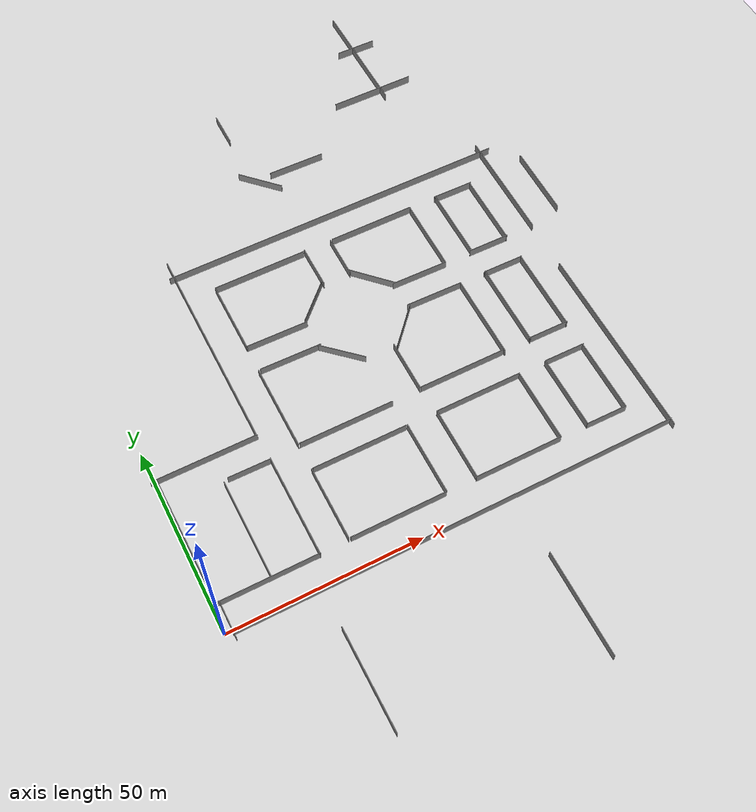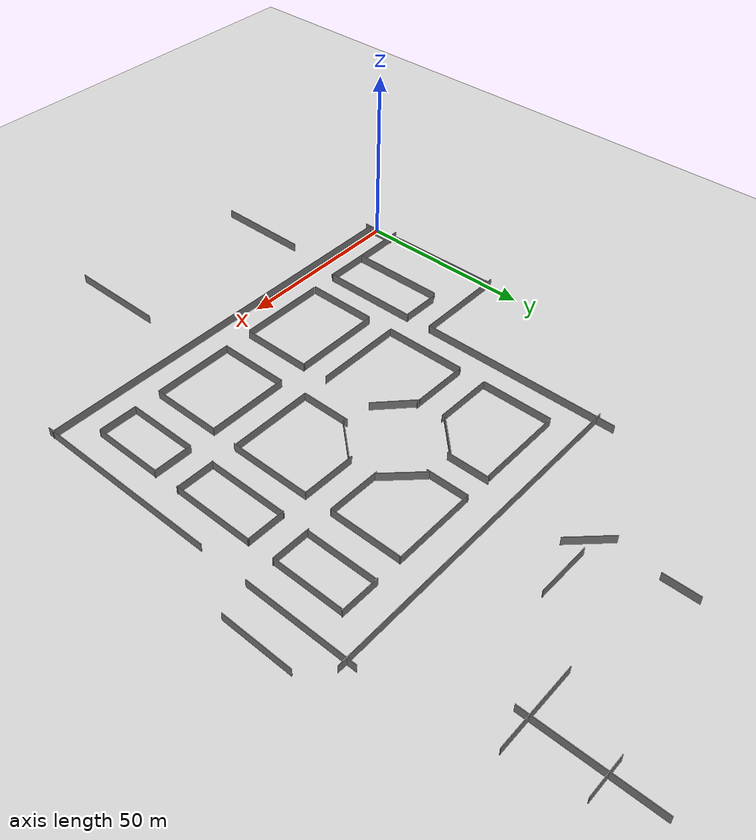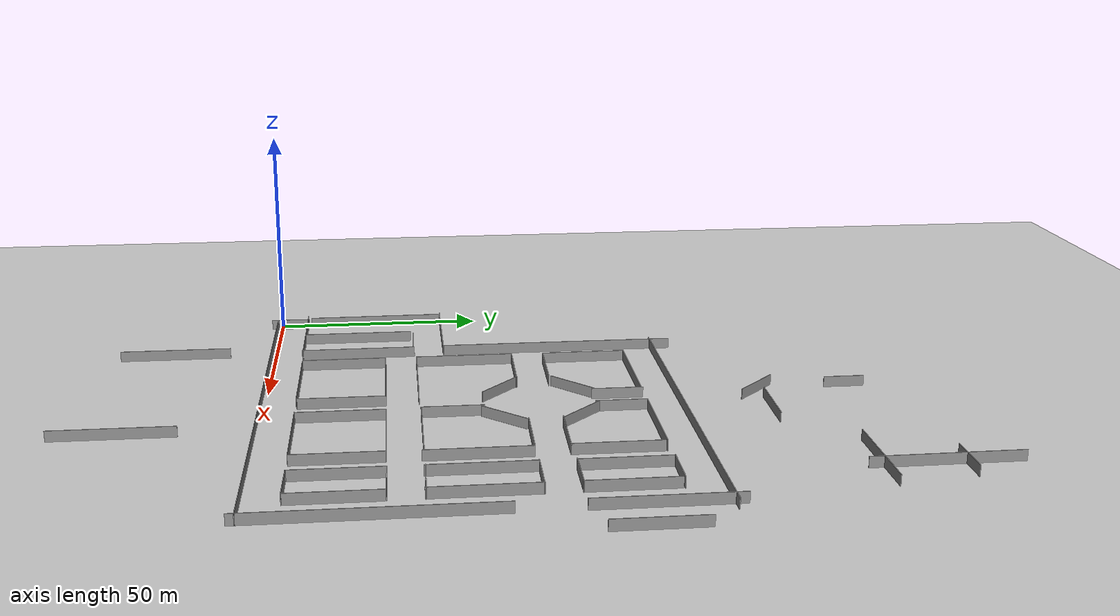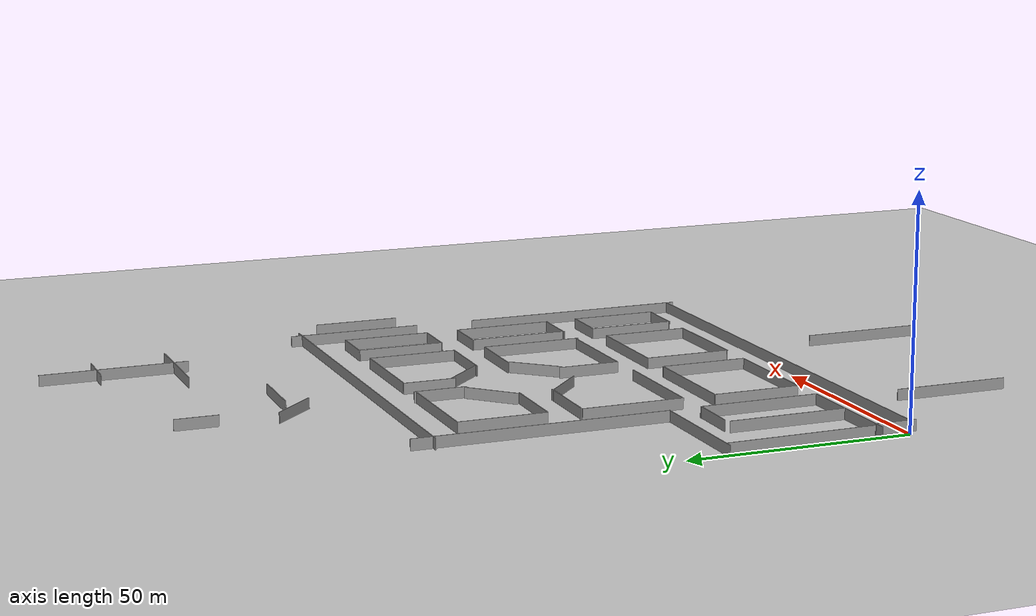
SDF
<sdf version="1.6">
 <world name="default">
  <light name="sun" type="directional">
   <pose>0 0 10 0 -0 0</pose>
   <diffuse>0.8 0.8 0.8 1</diffuse>
   <specular>0.2 0.2 0.2 1</specular>
   <attenuation>
    <range>1000</range>
    <constant>0.9</constant>
    <linear>0.01</linear>
    <quadratic>0.001</quadratic>
   </attenuation>
   <direction>-0.5 0.1 -0.9</direction>
  </light>
  <model name="ground_plane">
   <static>1</static>
   <link name="link">
    <collision name="collision">
     <geometry><plane><normal>0 0 1</normal><size>100 100</size></plane></geometry>
     <surface>
      <contact><collide_bitmask>65535</collide_bitmask></contact>
      <friction><ode><mu>100</mu><mu2>50</mu2></ode></friction>
     </surface>
    </collision>
    <visual name="visual">
     <cast_shadows>0</cast_shadows>
     <geometry><plane><normal>0 0 1</normal><size>100 100</size></plane></geometry>
     <material>
      <script><uri>file://media/materials/scripts/gazebo.material</uri><name>Gazebo/Grey</name></script>
     </material>
    </visual>
   </link>
  </model>
  <gravity>0 0 -9.8</gravity>
  <magnetic_field>6e-06 2.3e-05 -4.2e-05</magnetic_field>
  <atmosphere type="adiabatic"/>
  <physics name="default_physics" default="0" type="ode">
   <max_step_size>0.001</max_step_size>
   <real_time_factor>1</real_time_factor>
   <real_time_update_rate>1000</real_time_update_rate>
  </physics>
  <scene><ambient>0.4 0.4 0.4 1</ambient><background>0.7 0.7 0.7 1</background><shadows>1</shadows></scene>
  <audio><device>default</device></audio>
  <spherical_coordinates>
   <surface_model>EARTH_WGS84</surface_model>
   <latitude_deg>0</latitude_deg>
   <longitude_deg>0</longitude_deg>
   <elevation>0</elevation>
   <heading_deg>0</heading_deg>
  </spherical_coordinates>
  <model name="en_uzun_duvar2_clone">
   <link name="Wall_2">
    <inertial>
     <inertia><ixx>0</ixx><ixy>0</ixy><ixz>0</ixz><iyy>0</iyy><iyz>0</iyz><izz>0</izz></inertia>
     <mass>0</mass>
    </inertial>
    <visual name="Wall_2_Visual">
     <pose>0 0 1.25 0 -0 0</pose>
     <geometry><box><size>94.4523 0.15 2.5</size></box></geometry>
     <material>
      <script><uri>file://media/materials/scripts/gazebo.material</uri><name>Gazebo/Grey</name></script>
      <ambient>1 1 1 1</ambient>
     </material>
     <meta><layer>0</layer></meta>
    </visual>
    <collision name="Wall_2_Collision">
     <pose>0 0 1.25 0 -0 0</pose>
     <geometry><box><size>94.4523 0.15 2.5</size></box></geometry>
     <surface>
      <friction>
       <ode><mu>1</mu><mu2>1</mu2><fdir1>0 0 0</fdir1><slip1>0</slip1><slip2>0</slip2></ode>
       <torsional>
        <coefficient>1</coefficient>
        <patch_radius>0</patch_radius>
        <surface_radius>0</surface_radius>
        <use_patch_radius>1</use_patch_radius>
        <ode><slip>0</slip></ode>
       </torsional>
      </friction>
      <bounce><restitution_coefficient>0</restitution_coefficient><threshold>1e+06</threshold></bounce>
      <contact>
       <collide_without_contact>0</collide_without_contact>
       <collide_without_contact_bitmask>1</collide_without_contact_bitmask>
       <collide_bitmask>1</collide_bitmask>
       <ode>
        <soft_cfm>0</soft_cfm>
        <soft_erp>0.2</soft_erp>
        <kp>1e+13</kp>
        <kd>1</kd>
        <max_vel>0.01</max_vel>
        <min_depth>0</min_depth>
       </ode>
       <bullet>
        <split_impulse>1</split_impulse>
        <split_impulse_penetration_threshold>-0.01</split_impulse_penetration_threshold>
        <soft_cfm>0</soft_cfm>
        <soft_erp>0.2</soft_erp>
        <kp>1e+13</kp>
        <kd>1</kd>
       </bullet>
      </contact>
     </surface>
    </collision>
   </link>
   <static>1</static>
   <pose>72.3354 92.6336 0 0 -0 0</pose>
  </model>
  <model name="en_uzun_duvar2_clone_1">
   <link name="Wall_2">
    <pose>3.61471 -1e-06 0 0 -0 0</pose>
    <inertial>
     <inertia><ixx>0</ixx><ixy>0</ixy><ixz>0</ixz><iyy>0</iyy><iyz>0</iyz><izz>0</izz></inertia>
     <mass>0</mass>
    </inertial>
    <visual name="Wall_2_Visual">
     <pose>0 0 1.25 0 -0 0</pose>
     <geometry><box><size>56.4597 0.15 2.5</size></box></geometry>
     <material>
      <script><uri>file://media/materials/scripts/gazebo.material</uri><name>Gazebo/Grey</name></script>
      <ambient>1 1 1 1</ambient>
     </material>
     <meta><layer>0</layer></meta>
    </visual>
    <collision name="Wall_2_Collision">
     <pose>0 0 1.25 0 -0 0</pose>
     <geometry><box><size>56.4597 0.15 2.5</size></box></geometry>
     <surface>
      <friction>
       <ode><mu>1</mu><mu2>1</mu2><fdir1>0 0 0</fdir1><slip1>0</slip1><slip2>0</slip2></ode>
       <torsional>
        <coefficient>1</coefficient>
        <patch_radius>0</patch_radius>
        <surface_radius>0</surface_radius>
        <use_patch_radius>1</use_patch_radius>
        <ode><slip>0</slip></ode>
       </torsional>
      </friction>
      <bounce><restitution_coefficient>0</restitution_coefficient><threshold>1e+06</threshold></bounce>
      <contact>
       <collide_without_contact>0</collide_without_contact>
       <collide_without_contact_bitmask>1</collide_without_contact_bitmask>
       <collide_bitmask>1</collide_bitmask>
       <ode>
        <soft_cfm>0</soft_cfm>
        <soft_erp>0.2</soft_erp>
        <kp>1e+13</kp>
        <kd>1</kd>
        <max_vel>0.01</max_vel>
        <min_depth>0</min_depth>
       </ode>
       <bullet>
        <split_impulse>1</split_impulse>
        <split_impulse_penetration_threshold>-0.01</split_impulse_penetration_threshold>
        <soft_cfm>0</soft_cfm>
        <soft_erp>0.2</soft_erp>
        <kp>1e+13</kp>
        <kd>1</kd>
       </bullet>
      </contact>
     </surface>
    </collision>
   </link>
   <static>1</static>
   <pose>26.4078 65.6433 0 0 -0 1.57059</pose>
  </model>
  <model name="en_uzun_duvar2_clone_0">
   <link name="Wall_2">
    <pose>-3.83698 -0.045591 0 0 -0 0</pose>
    <inertial>
     <inertia><ixx>0</ixx><ixy>0</ixy><ixz>0</ixz><iyy>0</iyy><iyz>0</iyz><izz>0</izz></inertia>
     <mass>0</mass>
    </inertial>
    <visual name="Wall_2_Visual">
     <pose>0 0 1.25 0 -0 0</pose>
     <geometry><box><size>53.2897 0.15 2.5</size></box></geometry>
     <material>
      <script><uri>file://media/materials/scripts/gazebo.material</uri><name>Gazebo/Grey</name></script>
      <ambient>1 1 1 1</ambient>
     </material>
     <meta><layer>0</layer></meta>
    </visual>
    <collision name="Wall_2_Collision">
     <pose>0 0 1.25 0 -0 0</pose>
     <geometry><box><size>53.2897 0.15 2.5</size></box></geometry>
     <surface>
      <friction>
       <ode><mu>1</mu><mu2>1</mu2><fdir1>0 0 0</fdir1><slip1>0</slip1><slip2>0</slip2></ode>
       <torsional>
        <coefficient>1</coefficient>
        <patch_radius>0</patch_radius>
        <surface_radius>0</surface_radius>
        <use_patch_radius>1</use_patch_radius>
        <ode><slip>0</slip></ode>
       </torsional>
      </friction>
      <bounce><restitution_coefficient>0</restitution_coefficient><threshold>1e+06</threshold></bounce>
      <contact>
       <collide_without_contact>0</collide_without_contact>
       <collide_without_contact_bitmask>1</collide_without_contact_bitmask>
       <collide_bitmask>1</collide_bitmask>
       <ode>
        <soft_cfm>0</soft_cfm>
        <soft_erp>0.2</soft_erp>
        <kp>1e+13</kp>
        <kd>1</kd>
        <max_vel>0.01</max_vel>
        <min_depth>0</min_depth>
       </ode>
       <bullet>
        <split_impulse>1</split_impulse>
        <split_impulse_penetration_threshold>-0.01</split_impulse_penetration_threshold>
        <soft_cfm>0</soft_cfm>
        <soft_erp>0.2</soft_erp>
        <kp>1e+13</kp>
        <kd>1</kd>
       </bullet>
      </contact>
     </surface>
    </collision>
   </link>
   <static>1</static>
   <pose>116.717 27.7255 0 0 -0 1.57186</pose>
  </model>
  <model name="en_uzun_duvar2">
   <link name="Wall_2">
    <pose>1.00398 -0 0 0 -0 0</pose>
    <inertial>
     <inertia><ixx>0</ixx><ixy>0</ixy><ixz>0</ixz><iyy>0</iyy><iyz>0</iyz><izz>0</izz></inertia>
     <mass>0</mass>
    </inertial>
    <visual name="Wall_2_Visual">
     <pose>0 0 1.25 0 -0 0</pose>
     <geometry><box><size>115.363 0.15 2.5</size></box></geometry>
     <material>
      <script><uri>file://media/materials/scripts/gazebo.material</uri><name>Gazebo/Grey</name></script>
      <ambient>1 1 1 1</ambient>
     </material>
     <meta><layer>0</layer></meta>
    </visual>
    <collision name="Wall_2_Collision">
     <pose>0 0 1.25 0 -0 0</pose>
     <geometry><box><size>115.363 0.15 2.5</size></box></geometry>
     <surface>
      <friction>
       <ode><mu>1</mu><mu2>1</mu2><fdir1>0 0 0</fdir1><slip1>0</slip1><slip2>0</slip2></ode>
       <torsional>
        <coefficient>1</coefficient>
        <patch_radius>0</patch_radius>
        <surface_radius>0</surface_radius>
        <use_patch_radius>1</use_patch_radius>
        <ode><slip>0</slip></ode>
       </torsional>
      </friction>
      <bounce><restitution_coefficient>0</restitution_coefficient><threshold>1e+06</threshold></bounce>
      <contact>
       <collide_without_contact>0</collide_without_contact>
       <collide_without_contact_bitmask>1</collide_without_contact_bitmask>
       <collide_bitmask>1</collide_bitmask>
       <ode>
        <soft_cfm>0</soft_cfm>
        <soft_erp>0.2</soft_erp>
        <kp>1e+13</kp>
        <kd>1</kd>
        <max_vel>0.01</max_vel>
        <min_depth>0</min_depth>
       </ode>
       <bullet>
        <split_impulse>1</split_impulse>
        <split_impulse_penetration_threshold>-0.01</split_impulse_penetration_threshold>
        <soft_cfm>0</soft_cfm>
        <soft_erp>0.2</soft_erp>
        <kp>1e+13</kp>
        <kd>1</kd>
       </bullet>
      </contact>
     </surface>
    </collision>
   </link>
   <static>1</static>
   <pose>58.3673 -1.05458 0 0 -0 0</pose>
  </model>
  <model name="en_uzun_duvar2_clone_1_clone">
   <link name="Wall_2">
    <pose>10.2656 7.53235 0 0 -0 0</pose>
    <inertial>
     <inertia><ixx>0</ixx><ixy>0</ixy><ixz>0</ixz><iyy>0</iyy><iyz>0</iyz><izz>0</izz></inertia>
     <mass>0</mass>
    </inertial>
    <visual name="Wall_2_Visual">
     <pose>0 0 1.25 0 -0 0</pose>
     <geometry><box><size>30.968 0.15 2.5</size></box></geometry>
     <material>
      <script><uri>file://media/materials/scripts/gazebo.material</uri><name>Gazebo/Grey</name></script>
      <ambient>1 1 1 1</ambient>
     </material>
     <meta><layer>0</layer></meta>
    </visual>
    <collision name="Wall_2_Collision">
     <pose>0 0 1.25 0 -0 0</pose>
     <geometry><box><size>30.968 0.15 2.5</size></box></geometry>
     <surface>
      <friction>
       <ode><mu>1</mu><mu2>1</mu2><fdir1>0 0 0</fdir1><slip1>0</slip1><slip2>0</slip2></ode>
       <torsional>
        <coefficient>1</coefficient>
        <patch_radius>0</patch_radius>
        <surface_radius>0</surface_radius>
        <use_patch_radius>1</use_patch_radius>
        <ode><slip>0</slip></ode>
       </torsional>
      </friction>
      <bounce><restitution_coefficient>0</restitution_coefficient><threshold>1e+06</threshold></bounce>
      <contact>
       <collide_without_contact>0</collide_without_contact>
       <collide_without_contact_bitmask>1</collide_without_contact_bitmask>
       <collide_bitmask>1</collide_bitmask>
       <ode>
        <soft_cfm>0</soft_cfm>
        <soft_erp>0.2</soft_erp>
        <kp>1e+13</kp>
        <kd>1</kd>
        <max_vel>0.01</max_vel>
        <min_depth>0</min_depth>
       </ode>
       <bullet>
        <split_impulse>1</split_impulse>
        <split_impulse_penetration_threshold>-0.01</split_impulse_penetration_threshold>
        <soft_cfm>0</soft_cfm>
        <soft_erp>0.2</soft_erp>
        <kp>1e+13</kp>
        <kd>1</kd>
       </bullet>
      </contact>
     </surface>
    </collision>
   </link>
   <static>1</static>
   <pose>124.423 69.5169 0 0 -0 1.57059</pose>
  </model>
  <model name="en_uzun_duvar2_clone_1_clone_clone">
   <link name="Wall_2">
    <pose>10.2656 7.53235 0 0 -0 0</pose>
    <inertial>
     <inertia><ixx>0</ixx><ixy>0</ixy><ixz>0</ixz><iyy>0</iyy><iyz>0</iyz><izz>0</izz></inertia>
     <mass>0</mass>
    </inertial>
    <visual name="Wall_2_Visual">
     <pose>0 0 1.25 0 -0 0</pose>
     <geometry><box><size>19.779 0.15 2.5</size></box></geometry>
     <material>
      <script><uri>file://media/materials/scripts/gazebo.material</uri><name>Gazebo/Grey</name></script>
      <ambient>1 1 1 1</ambient>
     </material>
     <meta><layer>0</layer></meta>
    </visual>
    <collision name="Wall_2_Collision">
     <pose>0 0 1.25 0 -0 0</pose>
     <geometry><box><size>19.779 0.15 2.5</size></box></geometry>
     <surface>
      <friction>
       <ode><mu>1</mu><mu2>1</mu2><fdir1>0 0 0</fdir1><slip1>0</slip1><slip2>0</slip2></ode>
       <torsional>
        <coefficient>1</coefficient>
        <patch_radius>0</patch_radius>
        <surface_radius>0</surface_radius>
        <use_patch_radius>1</use_patch_radius>
        <ode><slip>0</slip></ode>
       </torsional>
      </friction>
      <bounce><restitution_coefficient>0</restitution_coefficient><threshold>1e+06</threshold></bounce>
      <contact>
       <collide_without_contact>0</collide_without_contact>
       <collide_without_contact_bitmask>1</collide_without_contact_bitmask>
       <collide_bitmask>1</collide_bitmask>
       <ode>
        <soft_cfm>0</soft_cfm>
        <soft_erp>0.2</soft_erp>
        <kp>1e+13</kp>
        <kd>1</kd>
        <max_vel>0.01</max_vel>
        <min_depth>0</min_depth>
       </ode>
       <bullet>
        <split_impulse>1</split_impulse>
        <split_impulse_penetration_threshold>-0.01</split_impulse_penetration_threshold>
        <soft_cfm>0</soft_cfm>
        <soft_erp>0.2</soft_erp>
        <kp>1e+13</kp>
        <kd>1</kd>
       </bullet>
      </contact>
     </surface>
    </collision>
   </link>
   <static>1</static>
   <pose>133.526 66.2954 0 0 -0 1.57059</pose>
  </model>
  <model name="en_uzun_duvar2_clone_1_clone_clone_clone_0">
   <link name="Wall_2">
    <pose>10.2656 7.53235 0 0 -0 0</pose>
    <inertial>
     <inertia><ixx>0</ixx><ixy>0</ixy><ixz>0</ixz><iyy>0</iyy><iyz>0</iyz><izz>0</izz></inertia>
     <mass>0</mass>
    </inertial>
    <visual name="Wall_2_Visual">
     <pose>0 0 1.25 0 -0 0</pose>
     <geometry><box><size>19.779 0.15 2.5</size></box></geometry>
     <material>
      <script><uri>file://media/materials/scripts/gazebo.material</uri><name>Gazebo/Grey</name></script>
      <ambient>1 1 1 1</ambient>
     </material>
     <meta><layer>0</layer></meta>
    </visual>
    <collision name="Wall_2_Collision">
     <pose>0 0 1.25 0 -0 0</pose>
     <geometry><box><size>19.779 0.15 2.5</size></box></geometry>
     <surface>
      <friction>
       <ode><mu>1</mu><mu2>1</mu2><fdir1>0 0 0</fdir1><slip1>0</slip1><slip2>0</slip2></ode>
       <torsional>
        <coefficient>1</coefficient>
        <patch_radius>0</patch_radius>
        <surface_radius>0</surface_radius>
        <use_patch_radius>1</use_patch_radius>
        <ode><slip>0</slip></ode>
       </torsional>
      </friction>
      <bounce><restitution_coefficient>0</restitution_coefficient><threshold>1e+06</threshold></bounce>
      <contact>
       <collide_without_contact>0</collide_without_contact>
       <collide_without_contact_bitmask>1</collide_without_contact_bitmask>
       <collide_bitmask>1</collide_bitmask>
       <ode>
        <soft_cfm>0</soft_cfm>
        <soft_erp>0.2</soft_erp>
        <kp>1e+13</kp>
        <kd>1</kd>
        <max_vel>0.01</max_vel>
        <min_depth>0</min_depth>
       </ode>
       <bullet>
        <split_impulse>1</split_impulse>
        <split_impulse_penetration_threshold>-0.01</split_impulse_penetration_threshold>
        <soft_cfm>0</soft_cfm>
        <soft_erp>0.2</soft_erp>
        <kp>1e+13</kp>
        <kd>1</kd>
       </bullet>
      </contact>
     </surface>
    </collision>
   </link>
   <static>1</static>
   <pose>116.494 64.1139 0 0 -0 1.57059</pose>
  </model>
  <model name="en_uzun_duvar2_clone_1_clone_clone_clone_1">
   <link name="Wall_2">
    <pose>10.2656 7.53235 0 0 -0 0</pose>
    <inertial>
     <inertia><ixx>0</ixx><ixy>0</ixy><ixz>0</ixz><iyy>0</iyy><iyz>0</iyz><izz>0</izz></inertia>
     <mass>0</mass>
    </inertial>
    <visual name="Wall_2_Visual">
     <pose>0 0 1.25 0 -0 0</pose>
     <geometry><box><size>19.779 0.15 2.5</size></box></geometry>
     <material>
      <script><uri>file://media/materials/scripts/gazebo.material</uri><name>Gazebo/Grey</name></script>
      <ambient>1 1 1 1</ambient>
     </material>
     <meta><layer>0</layer></meta>
    </visual>
    <collision name="Wall_2_Collision">
     <pose>0 0 1.25 0 -0 0</pose>
     <geometry><box><size>19.779 0.15 2.5</size></box></geometry>
     <surface>
      <friction>
       <ode><mu>1</mu><mu2>1</mu2><fdir1>0 0 0</fdir1><slip1>0</slip1><slip2>0</slip2></ode>
       <torsional>
        <coefficient>1</coefficient>
        <patch_radius>0</patch_radius>
        <surface_radius>0</surface_radius>
        <use_patch_radius>1</use_patch_radius>
        <ode><slip>0</slip></ode>
       </torsional>
      </friction>
      <bounce><restitution_coefficient>0</restitution_coefficient><threshold>1e+06</threshold></bounce>
      <contact>
       <collide_without_contact>0</collide_without_contact>
       <collide_without_contact_bitmask>1</collide_without_contact_bitmask>
       <collide_bitmask>1</collide_bitmask>
       <ode>
        <soft_cfm>0</soft_cfm>
        <soft_erp>0.2</soft_erp>
        <kp>1e+13</kp>
        <kd>1</kd>
        <max_vel>0.01</max_vel>
        <min_depth>0</min_depth>
       </ode>
       <bullet>
        <split_impulse>1</split_impulse>
        <split_impulse_penetration_threshold>-0.01</split_impulse_penetration_threshold>
        <soft_cfm>0</soft_cfm>
        <soft_erp>0.2</soft_erp>
        <kp>1e+13</kp>
        <kd>1</kd>
       </bullet>
      </contact>
     </surface>
    </collision>
   </link>
   <static>1</static>
   <pose>106.131 64.4436 0 0 -0 1.57059</pose>
  </model>
  <model name="en_uzun_duvar2_clone_1_clone_clone_clone_2">
   <link name="Wall_2">
    <pose>10.2656 7.53235 0 0 -0 0</pose>
    <inertial>
     <inertia><ixx>0</ixx><ixy>0</ixy><ixz>0</ixz><iyy>0</iyy><iyz>0</iyz><izz>0</izz></inertia>
     <mass>0</mass>
    </inertial>
    <visual name="Wall_2_Visual">
     <pose>0 0 1.25 0 -0 0</pose>
     <geometry><box><size>19.779 0.15 2.5</size></box></geometry>
     <material>
      <script><uri>file://media/materials/scripts/gazebo.material</uri><name>Gazebo/Grey</name></script>
      <ambient>1 1 1 1</ambient>
     </material>
     <meta><layer>0</layer></meta>
    </visual>
    <collision name="Wall_2_Collision">
     <pose>0 0 1.25 0 -0 0</pose>
     <geometry><box><size>19.779 0.15 2.5</size></box></geometry>
     <surface>
      <friction>
       <ode><mu>1</mu><mu2>1</mu2><fdir1>0 0 0</fdir1><slip1>0</slip1><slip2>0</slip2></ode>
       <torsional>
        <coefficient>1</coefficient>
        <patch_radius>0</patch_radius>
        <surface_radius>0</surface_radius>
        <use_patch_radius>1</use_patch_radius>
        <ode><slip>0</slip></ode>
       </torsional>
      </friction>
      <bounce><restitution_coefficient>0</restitution_coefficient><threshold>1e+06</threshold></bounce>
      <contact>
       <collide_without_contact>0</collide_without_contact>
       <collide_without_contact_bitmask>1</collide_without_contact_bitmask>
       <collide_bitmask>1</collide_bitmask>
       <ode>
        <soft_cfm>0</soft_cfm>
        <soft_erp>0.2</soft_erp>
        <kp>1e+13</kp>
        <kd>1</kd>
        <max_vel>0.01</max_vel>
        <min_depth>0</min_depth>
       </ode>
       <bullet>
        <split_impulse>1</split_impulse>
        <split_impulse_penetration_threshold>-0.01</split_impulse_penetration_threshold>
        <soft_cfm>0</soft_cfm>
        <soft_erp>0.2</soft_erp>
        <kp>1e+13</kp>
        <kd>1</kd>
       </bullet>
      </contact>
     </surface>
    </collision>
   </link>
   <static>1</static>
   <pose>98.2776 64.2004 0 0 -0 1.57059</pose>
  </model>
  <model name="en_uzun_duvar2_clone_1_clone_clone_clone_3">
   <link name="Wall_2">
    <pose>10.2656 7.53235 0 0 -0 0</pose>
    <inertial>
     <inertia><ixx>0</ixx><ixy>0</ixy><ixz>0</ixz><iyy>0</iyy><iyz>0</iyz><izz>0</izz></inertia>
     <mass>0</mass>
    </inertial>
    <visual name="Wall_2_Visual">
     <pose>0 0 1.25 0 -0 0</pose>
     <geometry><box><size>19.779 0.15 2.5</size></box></geometry>
     <material>
      <script><uri>file://media/materials/scripts/gazebo.material</uri><name>Gazebo/Grey</name></script>
      <ambient>1 1 1 1</ambient>
     </material>
     <meta><layer>0</layer></meta>
    </visual>
    <collision name="Wall_2_Collision">
     <pose>0 0 1.25 0 -0 0</pose>
     <geometry><box><size>19.779 0.15 2.5</size></box></geometry>
     <surface>
      <friction>
       <ode><mu>1</mu><mu2>1</mu2><fdir1>0 0 0</fdir1><slip1>0</slip1><slip2>0</slip2></ode>
       <torsional>
        <coefficient>1</coefficient>
        <patch_radius>0</patch_radius>
        <surface_radius>0</surface_radius>
        <use_patch_radius>1</use_patch_radius>
        <ode><slip>0</slip></ode>
       </torsional>
      </friction>
      <bounce><restitution_coefficient>0</restitution_coefficient><threshold>1e+06</threshold></bounce>
      <contact>
       <collide_without_contact>0</collide_without_contact>
       <collide_without_contact_bitmask>1</collide_without_contact_bitmask>
       <collide_bitmask>1</collide_bitmask>
       <ode>
        <soft_cfm>0</soft_cfm>
        <soft_erp>0.2</soft_erp>
        <kp>1e+13</kp>
        <kd>1</kd>
        <max_vel>0.01</max_vel>
        <min_depth>0</min_depth>
       </ode>
       <bullet>
        <split_impulse>1</split_impulse>
        <split_impulse_penetration_threshold>-0.01</split_impulse_penetration_threshold>
        <soft_cfm>0</soft_cfm>
        <soft_erp>0.2</soft_erp>
        <kp>1e+13</kp>
        <kd>1</kd>
       </bullet>
      </contact>
     </surface>
    </collision>
   </link>
   <static>1</static>
   <pose>116.58 6.45625 0 0 -0 1.57059</pose>
  </model>
  <model name="en_uzun_duvar2_clone_1_clone_clone_clone_5">
   <link name="Wall_2">
    <pose>10.2656 7.53235 0 0 -0 0</pose>
    <inertial>
     <inertia><ixx>0</ixx><ixy>0</ixy><ixz>0</ixz><iyy>0</iyy><iyz>0</iyz><izz>0</izz></inertia>
     <mass>0</mass>
    </inertial>
    <visual name="Wall_2_Visual">
     <pose>0 0 1.25 0 -0 0</pose>
     <geometry><box><size>19.779 0.15 2.5</size></box></geometry>
     <material>
      <script><uri>file://media/materials/scripts/gazebo.material</uri><name>Gazebo/Grey</name></script>
      <ambient>1 1 1 1</ambient>
     </material>
     <meta><layer>0</layer></meta>
    </visual>
    <collision name="Wall_2_Collision">
     <pose>0 0 1.25 0 -0 0</pose>
     <geometry><box><size>19.779 0.15 2.5</size></box></geometry>
     <surface>
      <friction>
       <ode><mu>1</mu><mu2>1</mu2><fdir1>0 0 0</fdir1><slip1>0</slip1><slip2>0</slip2></ode>
       <torsional>
        <coefficient>1</coefficient>
        <patch_radius>0</patch_radius>
        <surface_radius>0</surface_radius>
        <use_patch_radius>1</use_patch_radius>
        <ode><slip>0</slip></ode>
       </torsional>
      </friction>
      <bounce><restitution_coefficient>0</restitution_coefficient><threshold>1e+06</threshold></bounce>
      <contact>
       <collide_without_contact>0</collide_without_contact>
       <collide_without_contact_bitmask>1</collide_without_contact_bitmask>
       <collide_bitmask>1</collide_bitmask>
       <ode>
        <soft_cfm>0</soft_cfm>
        <soft_erp>0.2</soft_erp>
        <kp>1e+13</kp>
        <kd>1</kd>
        <max_vel>0.01</max_vel>
        <min_depth>0</min_depth>
       </ode>
       <bullet>
        <split_impulse>1</split_impulse>
        <split_impulse_penetration_threshold>-0.01</split_impulse_penetration_threshold>
        <soft_cfm>0</soft_cfm>
        <soft_erp>0.2</soft_erp>
        <kp>1e+13</kp>
        <kd>1</kd>
       </bullet>
      </contact>
     </surface>
    </collision>
   </link>
   <static>1</static>
   <pose>41.972 64.4212 0 0 -0 1.57059</pose>
  </model>
  <model name="en_uzun_duvar2_clone_1_clone_clone_clone_7">
   <link name="Wall_2">
    <pose>10.2656 7.53235 0 0 -0 0</pose>
    <inertial>
     <inertia><ixx>0</ixx><ixy>0</ixy><ixz>0</ixz><iyy>0</iyy><iyz>0</iyz><izz>0</izz></inertia>
     <mass>0</mass>
    </inertial>
    <visual name="Wall_2_Visual">
     <pose>0 0 1.25 0 -0 0</pose>
     <geometry><box><size>19.779 0.15 2.5</size></box></geometry>
     <material>
      <script><uri>file://media/materials/scripts/gazebo.material</uri><name>Gazebo/Grey</name></script>
      <ambient>1 1 1 1</ambient>
     </material>
     <meta><layer>0</layer></meta>
    </visual>
    <collision name="Wall_2_Collision">
     <pose>0 0 1.25 0 -0 0</pose>
     <geometry><box><size>19.779 0.15 2.5</size></box></geometry>
     <surface>
      <friction>
       <ode><mu>1</mu><mu2>1</mu2><fdir1>0 0 0</fdir1><slip1>0</slip1><slip2>0</slip2></ode>
       <torsional>
        <coefficient>1</coefficient>
        <patch_radius>0</patch_radius>
        <surface_radius>0</surface_radius>
        <use_patch_radius>1</use_patch_radius>
        <ode><slip>0</slip></ode>
       </torsional>
      </friction>
      <bounce><restitution_coefficient>0</restitution_coefficient><threshold>1e+06</threshold></bounce>
      <contact>
       <collide_without_contact>0</collide_without_contact>
       <collide_without_contact_bitmask>1</collide_without_contact_bitmask>
       <collide_bitmask>1</collide_bitmask>
       <ode>
        <soft_cfm>0</soft_cfm>
        <soft_erp>0.2</soft_erp>
        <kp>1e+13</kp>
        <kd>1</kd>
        <max_vel>0.01</max_vel>
        <min_depth>0</min_depth>
       </ode>
       <bullet>
        <split_impulse>1</split_impulse>
        <split_impulse_penetration_threshold>-0.01</split_impulse_penetration_threshold>
        <soft_cfm>0</soft_cfm>
        <soft_erp>0.2</soft_erp>
        <kp>1e+13</kp>
        <kd>1</kd>
       </bullet>
      </contact>
     </surface>
    </collision>
   </link>
   <static>1</static>
   <pose>75.3393 6.51625 0 0 -0 1.57059</pose>
  </model>
  <model name="en_uzun_duvar2_clone_1_clone_clone_clone_8">
   <link name="Wall_2">
    <pose>10.2656 7.53235 0 0 -0 0</pose>
    <inertial>
     <inertia><ixx>0</ixx><ixy>0</ixy><ixz>0</ixz><iyy>0</iyy><iyz>0</iyz><izz>0</izz></inertia>
     <mass>0</mass>
    </inertial>
    <visual name="Wall_2_Visual">
     <pose>0 0 1.25 0 -0 0</pose>
     <geometry><box><size>19.779 0.15 2.5</size></box></geometry>
     <material>
      <script><uri>file://media/materials/scripts/gazebo.material</uri><name>Gazebo/Grey</name></script>
      <ambient>1 1 1 1</ambient>
     </material>
     <meta><layer>0</layer></meta>
    </visual>
    <collision name="Wall_2_Collision">
     <pose>0 0 1.25 0 -0 0</pose>
     <geometry><box><size>19.779 0.15 2.5</size></box></geometry>
     <surface>
      <friction>
       <ode><mu>1</mu><mu2>1</mu2><fdir1>0 0 0</fdir1><slip1>0</slip1><slip2>0</slip2></ode>
       <torsional>
        <coefficient>1</coefficient>
        <patch_radius>0</patch_radius>
        <surface_radius>0</surface_radius>
        <use_patch_radius>1</use_patch_radius>
        <ode><slip>0</slip></ode>
       </torsional>
      </friction>
      <bounce><restitution_coefficient>0</restitution_coefficient><threshold>1e+06</threshold></bounce>
      <contact>
       <collide_without_contact>0</collide_without_contact>
       <collide_without_contact_bitmask>1</collide_without_contact_bitmask>
       <collide_bitmask>1</collide_bitmask>
       <ode>
        <soft_cfm>0</soft_cfm>
        <soft_erp>0.2</soft_erp>
        <kp>1e+13</kp>
        <kd>1</kd>
        <max_vel>0.01</max_vel>
        <min_depth>0</min_depth>
       </ode>
       <bullet>
        <split_impulse>1</split_impulse>
        <split_impulse_penetration_threshold>-0.01</split_impulse_penetration_threshold>
        <soft_cfm>0</soft_cfm>
        <soft_erp>0.2</soft_erp>
        <kp>1e+13</kp>
        <kd>1</kd>
       </bullet>
      </contact>
     </surface>
    </collision>
   </link>
   <static>1</static>
   <pose>67.2329 6.66775 0 0 -0 1.57059</pose>
  </model>
  <model name="en_uzun_duvar2_clone_1_clone_clone_clone_9">
   <link name="Wall_2">
    <pose>10.2656 7.53235 0 0 -0 0</pose>
    <inertial>
     <inertia><ixx>0</ixx><ixy>0</ixy><ixz>0</ixz><iyy>0</iyy><iyz>0</iyz><izz>0</izz></inertia>
     <mass>0</mass>
    </inertial>
    <visual name="Wall_2_Visual">
     <pose>0 0 1.25 0 -0 0</pose>
     <geometry><box><size>19.779 0.15 2.5</size></box></geometry>
     <material>
      <script><uri>file://media/materials/scripts/gazebo.material</uri><name>Gazebo/Grey</name></script>
      <ambient>1 1 1 1</ambient>
     </material>
     <meta><layer>0</layer></meta>
    </visual>
    <collision name="Wall_2_Collision">
     <pose>0 0 1.25 0 -0 0</pose>
     <geometry><box><size>19.779 0.15 2.5</size></box></geometry>
     <surface>
      <friction>
       <ode><mu>1</mu><mu2>1</mu2><fdir1>0 0 0</fdir1><slip1>0</slip1><slip2>0</slip2></ode>
       <torsional>
        <coefficient>1</coefficient>
        <patch_radius>0</patch_radius>
        <surface_radius>0</surface_radius>
        <use_patch_radius>1</use_patch_radius>
        <ode><slip>0</slip></ode>
       </torsional>
      </friction>
      <bounce><restitution_coefficient>0</restitution_coefficient><threshold>1e+06</threshold></bounce>
      <contact>
       <collide_without_contact>0</collide_without_contact>
       <collide_without_contact_bitmask>1</collide_without_contact_bitmask>
       <collide_bitmask>1</collide_bitmask>
       <ode>
        <soft_cfm>0</soft_cfm>
        <soft_erp>0.2</soft_erp>
        <kp>1e+13</kp>
        <kd>1</kd>
        <max_vel>0.01</max_vel>
        <min_depth>0</min_depth>
       </ode>
       <bullet>
        <split_impulse>1</split_impulse>
        <split_impulse_penetration_threshold>-0.01</split_impulse_penetration_threshold>
        <soft_cfm>0</soft_cfm>
        <soft_erp>0.2</soft_erp>
        <kp>1e+13</kp>
        <kd>1</kd>
       </bullet>
      </contact>
     </surface>
    </collision>
   </link>
   <static>1</static>
   <pose>98.3279 6.51975 0 0 -0 1.57059</pose>
  </model>
  <model name="en_uzun_duvar2_clone_1_clone_clone_clone">
   <link name="Wall_2">
    <pose>9.82359 7.53236 0 0 -0 0</pose>
    <inertial>
     <inertia><ixx>0</ixx><ixy>0</ixy><ixz>0</ixz><iyy>0</iyy><iyz>0</iyz><izz>0</izz></inertia>
     <mass>0</mass>
    </inertial>
    <visual name="Wall_2_Visual">
     <pose>0 0 1.25 0 -0 0</pose>
     <geometry><box><size>11.0273 0.15 2.5</size></box></geometry>
     <material>
      <script><uri>file://media/materials/scripts/gazebo.material</uri><name>Gazebo/Grey</name></script>
      <ambient>1 1 1 1</ambient>
     </material>
     <meta><layer>0</layer></meta>
    </visual>
    <collision name="Wall_2_Collision">
     <pose>0 0 1.25 0 -0 0</pose>
     <geometry><box><size>11.0273 0.15 2.5</size></box></geometry>
     <surface>
      <friction>
       <ode><mu>1</mu><mu2>1</mu2><fdir1>0 0 0</fdir1><slip1>0</slip1><slip2>0</slip2></ode>
       <torsional>
        <coefficient>1</coefficient>
        <patch_radius>0</patch_radius>
        <surface_radius>0</surface_radius>
        <use_patch_radius>1</use_patch_radius>
        <ode><slip>0</slip></ode>
       </torsional>
      </friction>
      <bounce><restitution_coefficient>0</restitution_coefficient><threshold>1e+06</threshold></bounce>
      <contact>
       <collide_without_contact>0</collide_without_contact>
       <collide_without_contact_bitmask>1</collide_without_contact_bitmask>
       <collide_bitmask>1</collide_bitmask>
       <ode>
        <soft_cfm>0</soft_cfm>
        <soft_erp>0.2</soft_erp>
        <kp>1e+13</kp>
        <kd>1</kd>
        <max_vel>0.01</max_vel>
        <min_depth>0</min_depth>
       </ode>
       <bullet>
        <split_impulse>1</split_impulse>
        <split_impulse_penetration_threshold>-0.01</split_impulse_penetration_threshold>
        <soft_cfm>0</soft_cfm>
        <soft_erp>0.2</soft_erp>
        <kp>1e+13</kp>
        <kd>1</kd>
       </bullet>
      </contact>
     </surface>
    </collision>
   </link>
   <static>1</static>
   <pose>114.047 151.034 0 0 -0 3.13031</pose>
  </model>
  <model name="en_uzun_duvar2_clone_1_clone_clone_clone_clone_0">
   <link name="Wall_2">
    <pose>9.82359 7.53236 0 0 -0 0</pose>
    <inertial>
     <inertia><ixx>0</ixx><ixy>0</ixy><ixz>0</ixz><iyy>0</iyy><iyz>0</iyz><izz>0</izz></inertia>
     <mass>0</mass>
    </inertial>
    <visual name="Wall_2_Visual">
     <pose>0 0 1.25 0 -0 0</pose>
     <geometry><box><size>11.0273 0.15 2.5</size></box></geometry>
     <material>
      <script><uri>file://media/materials/scripts/gazebo.material</uri><name>Gazebo/Grey</name></script>
      <ambient>1 1 1 1</ambient>
     </material>
     <meta><layer>0</layer></meta>
    </visual>
    <collision name="Wall_2_Collision">
     <pose>0 0 1.25 0 -0 0</pose>
     <geometry><box><size>11.0273 0.15 2.5</size></box></geometry>
     <surface>
      <friction>
       <ode><mu>1</mu><mu2>1</mu2><fdir1>0 0 0</fdir1><slip1>0</slip1><slip2>0</slip2></ode>
       <torsional>
        <coefficient>1</coefficient>
        <patch_radius>0</patch_radius>
        <surface_radius>0</surface_radius>
        <use_patch_radius>1</use_patch_radius>
        <ode><slip>0</slip></ode>
       </torsional>
      </friction>
      <bounce><restitution_coefficient>0</restitution_coefficient><threshold>1e+06</threshold></bounce>
      <contact>
       <collide_without_contact>0</collide_without_contact>
       <collide_without_contact_bitmask>1</collide_without_contact_bitmask>
       <collide_bitmask>1</collide_bitmask>
       <ode>
        <soft_cfm>0</soft_cfm>
        <soft_erp>0.2</soft_erp>
        <kp>1e+13</kp>
        <kd>1</kd>
        <max_vel>0.01</max_vel>
        <min_depth>0</min_depth>
       </ode>
       <bullet>
        <split_impulse>1</split_impulse>
        <split_impulse_penetration_threshold>-0.01</split_impulse_penetration_threshold>
        <soft_cfm>0</soft_cfm>
        <soft_erp>0.2</soft_erp>
        <kp>1e+13</kp>
        <kd>1</kd>
       </bullet>
      </contact>
     </surface>
    </collision>
   </link>
   <static>1</static>
   <pose>113.523 64.4952 0 0 -0 3.13031</pose>
  </model>
  <model name="en_uzun_duvar2_clone_1_clone_clone_clone_clone_1">
   <link name="Wall_2">
    <pose>9.82359 7.53236 0 0 -0 0</pose>
    <inertial>
     <inertia><ixx>0</ixx><ixy>0</ixy><ixz>0</ixz><iyy>0</iyy><iyz>0</iyz><izz>0</izz></inertia>
     <mass>0</mass>
    </inertial>
    <visual name="Wall_2_Visual">
     <pose>0 0 1.25 0 -0 0</pose>
     <geometry><box><size>11.0273 0.15 2.5</size></box></geometry>
     <material>
      <script><uri>file://media/materials/scripts/gazebo.material</uri><name>Gazebo/Grey</name></script>
      <ambient>1 1 1 1</ambient>
     </material>
     <meta><layer>0</layer></meta>
    </visual>
    <collision name="Wall_2_Collision">
     <pose>0 0 1.25 0 -0 0</pose>
     <geometry><box><size>11.0273 0.15 2.5</size></box></geometry>
     <surface>
      <friction>
       <ode><mu>1</mu><mu2>1</mu2><fdir1>0 0 0</fdir1><slip1>0</slip1><slip2>0</slip2></ode>
       <torsional>
        <coefficient>1</coefficient>
        <patch_radius>0</patch_radius>
        <surface_radius>0</surface_radius>
        <use_patch_radius>1</use_patch_radius>
        <ode><slip>0</slip></ode>
       </torsional>
      </friction>
      <bounce><restitution_coefficient>0</restitution_coefficient><threshold>1e+06</threshold></bounce>
      <contact>
       <collide_without_contact>0</collide_without_contact>
       <collide_without_contact_bitmask>1</collide_without_contact_bitmask>
       <collide_bitmask>1</collide_bitmask>
       <ode>
        <soft_cfm>0</soft_cfm>
        <soft_erp>0.2</soft_erp>
        <kp>1e+13</kp>
        <kd>1</kd>
        <max_vel>0.01</max_vel>
        <min_depth>0</min_depth>
       </ode>
       <bullet>
        <split_impulse>1</split_impulse>
        <split_impulse_penetration_threshold>-0.01</split_impulse_penetration_threshold>
        <soft_cfm>0</soft_cfm>
        <soft_erp>0.2</soft_erp>
        <kp>1e+13</kp>
        <kd>1</kd>
       </bullet>
      </contact>
     </surface>
    </collision>
   </link>
   <static>1</static>
   <pose>113.712 34.1944 0 0 -0 3.13031</pose>
  </model>
  <model name="en_uzun_duvar2_clone_1_clone_clone_clone_clone_2">
   <link name="Wall_2">
    <pose>9.82359 7.53236 0 0 -0 0</pose>
    <inertial>
     <inertia><ixx>0</ixx><ixy>0</ixy><ixz>0</ixz><iyy>0</iyy><iyz>0</iyz><izz>0</izz></inertia>
     <mass>0</mass>
    </inertial>
    <visual name="Wall_2_Visual">
     <pose>0 0 1.25 0 -0 0</pose>
     <geometry><box><size>11.0273 0.15 2.5</size></box></geometry>
     <material>
      <script><uri>file://media/materials/scripts/gazebo.material</uri><name>Gazebo/Grey</name></script>
      <ambient>1 1 1 1</ambient>
     </material>
     <meta><layer>0</layer></meta>
    </visual>
    <collision name="Wall_2_Collision">
     <pose>0 0 1.25 0 -0 0</pose>
     <geometry><box><size>11.0273 0.15 2.5</size></box></geometry>
     <surface>
      <friction>
       <ode><mu>1</mu><mu2>1</mu2><fdir1>0 0 0</fdir1><slip1>0</slip1><slip2>0</slip2></ode>
       <torsional>
        <coefficient>1</coefficient>
        <patch_radius>0</patch_radius>
        <surface_radius>0</surface_radius>
        <use_patch_radius>1</use_patch_radius>
        <ode><slip>0</slip></ode>
       </torsional>
      </friction>
      <bounce><restitution_coefficient>0</restitution_coefficient><threshold>1e+06</threshold></bounce>
      <contact>
       <collide_without_contact>0</collide_without_contact>
       <collide_without_contact_bitmask>1</collide_without_contact_bitmask>
       <collide_bitmask>1</collide_bitmask>
       <ode>
        <soft_cfm>0</soft_cfm>
        <soft_erp>0.2</soft_erp>
        <kp>1e+13</kp>
        <kd>1</kd>
        <max_vel>0.01</max_vel>
        <min_depth>0</min_depth>
       </ode>
       <bullet>
        <split_impulse>1</split_impulse>
        <split_impulse_penetration_threshold>-0.01</split_impulse_penetration_threshold>
        <soft_cfm>0</soft_cfm>
        <soft_erp>0.2</soft_erp>
        <kp>1e+13</kp>
        <kd>1</kd>
       </bullet>
      </contact>
     </surface>
    </collision>
   </link>
   <static>1</static>
   <pose>113.659 41.7843 0 0 -0 3.13031</pose>
  </model>
  <model name="en_uzun_duvar2_clone_1_clone_clone_clone_clone_3">
   <link name="Wall_2">
    <pose>9.82359 7.53236 0 0 -0 0</pose>
    <inertial>
     <inertia><ixx>0</ixx><ixy>0</ixy><ixz>0</ixz><iyy>0</iyy><iyz>0</iyz><izz>0</izz></inertia>
     <mass>0</mass>
    </inertial>
    <visual name="Wall_2_Visual">
     <pose>0 0 1.25 0 -0 0</pose>
     <geometry><box><size>11.0273 0.15 2.5</size></box></geometry>
     <material>
      <script><uri>file://media/materials/scripts/gazebo.material</uri><name>Gazebo/Grey</name></script>
      <ambient>1 1 1 1</ambient>
     </material>
     <meta><layer>0</layer></meta>
    </visual>
    <collision name="Wall_2_Collision">
     <pose>0 0 1.25 0 -0 0</pose>
     <geometry><box><size>11.0273 0.15 2.5</size></box></geometry>
     <surface>
      <friction>
       <ode><mu>1</mu><mu2>1</mu2><fdir1>0 0 0</fdir1><slip1>0</slip1><slip2>0</slip2></ode>
       <torsional>
        <coefficient>1</coefficient>
        <patch_radius>0</patch_radius>
        <surface_radius>0</surface_radius>
        <use_patch_radius>1</use_patch_radius>
        <ode><slip>0</slip></ode>
       </torsional>
      </friction>
      <bounce><restitution_coefficient>0</restitution_coefficient><threshold>1e+06</threshold></bounce>
      <contact>
       <collide_without_contact>0</collide_without_contact>
       <collide_without_contact_bitmask>1</collide_without_contact_bitmask>
       <collide_bitmask>1</collide_bitmask>
       <ode>
        <soft_cfm>0</soft_cfm>
        <soft_erp>0.2</soft_erp>
        <kp>1e+13</kp>
        <kd>1</kd>
        <max_vel>0.01</max_vel>
        <min_depth>0</min_depth>
       </ode>
       <bullet>
        <split_impulse>1</split_impulse>
        <split_impulse_penetration_threshold>-0.01</split_impulse_penetration_threshold>
        <soft_cfm>0</soft_cfm>
        <soft_erp>0.2</soft_erp>
        <kp>1e+13</kp>
        <kd>1</kd>
       </bullet>
      </contact>
     </surface>
    </collision>
   </link>
   <static>1</static>
   <pose>113.605 14.3356 0 0 -0 3.13031</pose>
  </model>
  <model name="en_uzun_duvar2_clone_1_clone_clone_clone_clone_4">
   <link name="Wall_2">
    <pose>9.82359 7.53236 0 0 -0 0</pose>
    <inertial>
     <inertia><ixx>0</ixx><ixy>0</ixy><ixz>0</ixz><iyy>0</iyy><iyz>0</iyz><izz>0</izz></inertia>
     <mass>0</mass>
    </inertial>
    <visual name="Wall_2_Visual">
     <pose>0 0 1.25 0 -0 0</pose>
     <geometry><box><size>11.0273 0.15 2.5</size></box></geometry>
     <material>
      <script><uri>file://media/materials/scripts/gazebo.material</uri><name>Gazebo/Grey</name></script>
      <ambient>1 1 1 1</ambient>
     </material>
     <meta><layer>0</layer></meta>
    </visual>
    <collision name="Wall_2_Collision">
     <pose>0 0 1.25 0 -0 0</pose>
     <geometry><box><size>11.0273 0.15 2.5</size></box></geometry>
     <surface>
      <friction>
       <ode><mu>1</mu><mu2>1</mu2><fdir1>0 0 0</fdir1><slip1>0</slip1><slip2>0</slip2></ode>
       <torsional>
        <coefficient>1</coefficient>
        <patch_radius>0</patch_radius>
        <surface_radius>0</surface_radius>
        <use_patch_radius>1</use_patch_radius>
        <ode><slip>0</slip></ode>
       </torsional>
      </friction>
      <bounce><restitution_coefficient>0</restitution_coefficient><threshold>1e+06</threshold></bounce>
      <contact>
       <collide_without_contact>0</collide_without_contact>
       <collide_without_contact_bitmask>1</collide_without_contact_bitmask>
       <collide_bitmask>1</collide_bitmask>
       <ode>
        <soft_cfm>0</soft_cfm>
        <soft_erp>0.2</soft_erp>
        <kp>1e+13</kp>
        <kd>1</kd>
        <max_vel>0.01</max_vel>
        <min_depth>0</min_depth>
       </ode>
       <bullet>
        <split_impulse>1</split_impulse>
        <split_impulse_penetration_threshold>-0.01</split_impulse_penetration_threshold>
        <soft_cfm>0</soft_cfm>
        <soft_erp>0.2</soft_erp>
        <kp>1e+13</kp>
        <kd>1</kd>
       </bullet>
      </contact>
     </surface>
    </collision>
   </link>
   <static>1</static>
   <pose>113.592 72.0962 0 0 -0 3.13031</pose>
  </model>
  <model name="en_uzun_duvar2_clone_1_clone_clone_clone_10_clone">
   <link name="Wall_2">
    <pose>10.2656 7.53235 0 0 -0 0</pose>
    <inertial>
     <inertia><ixx>0</ixx><ixy>0</ixy><ixz>0</ixz><iyy>0</iyy><iyz>0</iyz><izz>0</izz></inertia>
     <mass>0</mass>
    </inertial>
    <visual name="Wall_2_Visual">
     <pose>0 0 1.25 0 -0 0</pose>
     <geometry><box><size>23.1013 0.15 2.5</size></box></geometry>
     <material>
      <script><uri>file://media/materials/scripts/gazebo.material</uri><name>Gazebo/Grey</name></script>
      <ambient>1 1 1 1</ambient>
     </material>
     <meta><layer>0</layer></meta>
    </visual>
    <collision name="Wall_2_Collision">
     <pose>0 0 1.25 0 -0 0</pose>
     <geometry><box><size>23.1013 0.15 2.5</size></box></geometry>
     <surface>
      <friction>
       <ode><mu>1</mu><mu2>1</mu2><fdir1>0 0 0</fdir1><slip1>0</slip1><slip2>0</slip2></ode>
       <torsional>
        <coefficient>1</coefficient>
        <patch_radius>0</patch_radius>
        <surface_radius>0</surface_radius>
        <use_patch_radius>1</use_patch_radius>
        <ode><slip>0</slip></ode>
       </torsional>
      </friction>
      <bounce><restitution_coefficient>0</restitution_coefficient><threshold>1e+06</threshold></bounce>
      <contact>
       <collide_without_contact>0</collide_without_contact>
       <collide_without_contact_bitmask>1</collide_without_contact_bitmask>
       <collide_bitmask>1</collide_bitmask>
       <ode>
        <soft_cfm>0</soft_cfm>
        <soft_erp>0.2</soft_erp>
        <kp>1e+13</kp>
        <kd>1</kd>
        <max_vel>0.01</max_vel>
        <min_depth>0</min_depth>
       </ode>
       <bullet>
        <split_impulse>1</split_impulse>
        <split_impulse_penetration_threshold>-0.01</split_impulse_penetration_threshold>
        <soft_cfm>0</soft_cfm>
        <soft_erp>0.2</soft_erp>
        <kp>1e+13</kp>
        <kd>1</kd>
       </bullet>
      </contact>
     </surface>
    </collision>
   </link>
   <static>1</static>
   <pose>116.467 35.3175 0 0 -0 1.57059</pose>
  </model>
  <model name="en_uzun_duvar2_clone_1_clone_clone_clone_10_clone_0">
   <link name="Wall_2">
    <pose>10.2656 7.53235 0 0 -0 0</pose>
    <inertial>
     <inertia><ixx>0</ixx><ixy>0</ixy><ixz>0</ixz><iyy>0</iyy><iyz>0</iyz><izz>0</izz></inertia>
     <mass>0</mass>
    </inertial>
    <visual name="Wall_2_Visual">
     <pose>0 0 1.25 0 -0 0</pose>
     <geometry><box><size>23.1013 0.15 2.5</size></box></geometry>
     <material>
      <script><uri>file://media/materials/scripts/gazebo.material</uri><name>Gazebo/Grey</name></script>
      <ambient>1 1 1 1</ambient>
     </material>
     <meta><layer>0</layer></meta>
    </visual>
    <collision name="Wall_2_Collision">
     <pose>0 0 1.25 0 -0 0</pose>
     <geometry><box><size>23.1013 0.15 2.5</size></box></geometry>
     <surface>
      <friction>
       <ode><mu>1</mu><mu2>1</mu2><fdir1>0 0 0</fdir1><slip1>0</slip1><slip2>0</slip2></ode>
       <torsional>
        <coefficient>1</coefficient>
        <patch_radius>0</patch_radius>
        <surface_radius>0</surface_radius>
        <use_patch_radius>1</use_patch_radius>
        <ode><slip>0</slip></ode>
       </torsional>
      </friction>
      <bounce><restitution_coefficient>0</restitution_coefficient><threshold>1e+06</threshold></bounce>
      <contact>
       <collide_without_contact>0</collide_without_contact>
       <collide_without_contact_bitmask>1</collide_without_contact_bitmask>
       <collide_bitmask>1</collide_bitmask>
       <ode>
        <soft_cfm>0</soft_cfm>
        <soft_erp>0.2</soft_erp>
        <kp>1e+13</kp>
        <kd>1</kd>
        <max_vel>0.01</max_vel>
        <min_depth>0</min_depth>
       </ode>
       <bullet>
        <split_impulse>1</split_impulse>
        <split_impulse_penetration_threshold>-0.01</split_impulse_penetration_threshold>
        <soft_cfm>0</soft_cfm>
        <soft_erp>0.2</soft_erp>
        <kp>1e+13</kp>
        <kd>1</kd>
       </bullet>
      </contact>
     </surface>
    </collision>
   </link>
   <static>1</static>
   <pose>105.933 35.4263 0 0 -0 1.57059</pose>
  </model>
  <model name="en_uzun_duvar2_clone_1_clone_clone_clone_10_clone_1">
   <link name="Wall_2">
    <pose>10.2656 7.53235 0 0 -0 0</pose>
    <inertial>
     <inertia><ixx>0</ixx><ixy>0</ixy><ixz>0</ixz><iyy>0</iyy><iyz>0</iyz><izz>0</izz></inertia>
     <mass>0</mass>
    </inertial>
    <visual name="Wall_2_Visual">
     <pose>0 0 1.25 0 -0 0</pose>
     <geometry><box><size>23.1013 0.15 2.5</size></box></geometry>
     <material>
      <script><uri>file://media/materials/scripts/gazebo.material</uri><name>Gazebo/Grey</name></script>
      <ambient>1 1 1 1</ambient>
     </material>
     <meta><layer>0</layer></meta>
    </visual>
    <collision name="Wall_2_Collision">
     <pose>0 0 1.25 0 -0 0</pose>
     <geometry><box><size>23.1013 0.15 2.5</size></box></geometry>
     <surface>
      <friction>
       <ode><mu>1</mu><mu2>1</mu2><fdir1>0 0 0</fdir1><slip1>0</slip1><slip2>0</slip2></ode>
       <torsional>
        <coefficient>1</coefficient>
        <patch_radius>0</patch_radius>
        <surface_radius>0</surface_radius>
        <use_patch_radius>1</use_patch_radius>
        <ode><slip>0</slip></ode>
       </torsional>
      </friction>
      <bounce><restitution_coefficient>0</restitution_coefficient><threshold>1e+06</threshold></bounce>
      <contact>
       <collide_without_contact>0</collide_without_contact>
       <collide_without_contact_bitmask>1</collide_without_contact_bitmask>
       <collide_bitmask>1</collide_bitmask>
       <ode>
        <soft_cfm>0</soft_cfm>
        <soft_erp>0.2</soft_erp>
        <kp>1e+13</kp>
        <kd>1</kd>
        <max_vel>0.01</max_vel>
        <min_depth>0</min_depth>
       </ode>
       <bullet>
        <split_impulse>1</split_impulse>
        <split_impulse_penetration_threshold>-0.01</split_impulse_penetration_threshold>
        <soft_cfm>0</soft_cfm>
        <soft_erp>0.2</soft_erp>
        <kp>1e+13</kp>
        <kd>1</kd>
       </bullet>
      </contact>
     </surface>
    </collision>
   </link>
   <static>1</static>
   <pose>98.5301 35.2119 0 0 -0 1.57059</pose>
  </model>
  <model name="en_uzun_duvar2_clone_1_clone_clone_clone_10_clone_2">
   <link name="Wall_2">
    <pose>10.2656 7.53235 0 0 -0 0</pose>
    <inertial>
     <inertia><ixx>0</ixx><ixy>0</ixy><ixz>0</ixz><iyy>0</iyy><iyz>0</iyz><izz>0</izz></inertia>
     <mass>0</mass>
    </inertial>
    <visual name="Wall_2_Visual">
     <pose>0 0 1.25 0 -0 0</pose>
     <geometry><box><size>23.1013 0.15 2.5</size></box></geometry>
     <material>
      <script><uri>file://media/materials/scripts/gazebo.material</uri><name>Gazebo/Grey</name></script>
      <ambient>1 1 1 1</ambient>
     </material>
     <meta><layer>0</layer></meta>
    </visual>
    <collision name="Wall_2_Collision">
     <pose>0 0 1.25 0 -0 0</pose>
     <geometry><box><size>23.1013 0.15 2.5</size></box></geometry>
     <surface>
      <friction>
       <ode><mu>1</mu><mu2>1</mu2><fdir1>0 0 0</fdir1><slip1>0</slip1><slip2>0</slip2></ode>
       <torsional>
        <coefficient>1</coefficient>
        <patch_radius>0</patch_radius>
        <surface_radius>0</surface_radius>
        <use_patch_radius>1</use_patch_radius>
        <ode><slip>0</slip></ode>
       </torsional>
      </friction>
      <bounce><restitution_coefficient>0</restitution_coefficient><threshold>1e+06</threshold></bounce>
      <contact>
       <collide_without_contact>0</collide_without_contact>
       <collide_without_contact_bitmask>1</collide_without_contact_bitmask>
       <collide_bitmask>1</collide_bitmask>
       <ode>
        <soft_cfm>0</soft_cfm>
        <soft_erp>0.2</soft_erp>
        <kp>1e+13</kp>
        <kd>1</kd>
        <max_vel>0.01</max_vel>
        <min_depth>0</min_depth>
       </ode>
       <bullet>
        <split_impulse>1</split_impulse>
        <split_impulse_penetration_threshold>-0.01</split_impulse_penetration_threshold>
        <soft_cfm>0</soft_cfm>
        <soft_erp>0.2</soft_erp>
        <kp>1e+13</kp>
        <kd>1</kd>
       </bullet>
      </contact>
     </surface>
    </collision>
   </link>
   <static>1</static>
   <pose>41.7465 35.4057 0 0 -0 1.57059</pose>
  </model>
  <model name="en_uzun_duvar2_clone_1_clone_clone_clone_6_clone">
   <link name="Wall_2">
    <pose>10.2656 7.53235 0 0 -0 0</pose>
    <inertial>
     <inertia><ixx>0</ixx><ixy>0</ixy><ixz>0</ixz><iyy>0</iyy><iyz>0</iyz><izz>0</izz></inertia>
     <mass>0</mass>
    </inertial>
    <visual name="Wall_2_Visual">
     <pose>0 0 1.25 0 -0 0</pose>
     <geometry><box><size>19.779 0.15 2.5</size></box></geometry>
     <material>
      <script><uri>file://media/materials/scripts/gazebo.material</uri><name>Gazebo/Grey</name></script>
      <ambient>1 1 1 1</ambient>
     </material>
     <meta><layer>0</layer></meta>
    </visual>
    <collision name="Wall_2_Collision">
     <pose>0 0 1.25 0 -0 0</pose>
     <geometry><box><size>19.779 0.15 2.5</size></box></geometry>
     <surface>
      <friction>
       <ode><mu>1</mu><mu2>1</mu2><fdir1>0 0 0</fdir1><slip1>0</slip1><slip2>0</slip2></ode>
       <torsional>
        <coefficient>1</coefficient>
        <patch_radius>0</patch_radius>
        <surface_radius>0</surface_radius>
        <use_patch_radius>1</use_patch_radius>
        <ode><slip>0</slip></ode>
       </torsional>
      </friction>
      <bounce><restitution_coefficient>0</restitution_coefficient><threshold>1e+06</threshold></bounce>
      <contact>
       <collide_without_contact>0</collide_without_contact>
       <collide_without_contact_bitmask>1</collide_without_contact_bitmask>
       <collide_bitmask>1</collide_bitmask>
       <ode>
        <soft_cfm>0</soft_cfm>
        <soft_erp>0.2</soft_erp>
        <kp>1e+13</kp>
        <kd>1</kd>
        <max_vel>0.01</max_vel>
        <min_depth>0</min_depth>
       </ode>
       <bullet>
        <split_impulse>1</split_impulse>
        <split_impulse_penetration_threshold>-0.01</split_impulse_penetration_threshold>
        <soft_cfm>0</soft_cfm>
        <soft_erp>0.2</soft_erp>
        <kp>1e+13</kp>
        <kd>1</kd>
       </bullet>
      </contact>
     </surface>
    </collision>
   </link>
   <static>1</static>
   <pose>41.731 6.60135 0 0 -0 1.57059</pose>
  </model>
  <model name="en_uzun_duvar2_clone_1_clone_clone_clone_10_clone_3_clone_0">
   <link name="Wall_2">
    <pose>10.2656 7.53235 0 0 -0 0</pose>
    <inertial>
     <inertia><ixx>0</ixx><ixy>0</ixy><ixz>0</ixz><iyy>0</iyy><iyz>0</iyz><izz>0</izz></inertia>
     <mass>0</mass>
    </inertial>
    <visual name="Wall_2_Visual">
     <pose>0 0 1.25 0 -0 0</pose>
     <geometry><box><size>14.1147 0.15 2.5</size></box></geometry>
     <material>
      <script><uri>file://media/materials/scripts/gazebo.material</uri><name>Gazebo/Grey</name></script>
      <ambient>1 1 1 1</ambient>
     </material>
     <meta><layer>0</layer></meta>
    </visual>
    <collision name="Wall_2_Collision">
     <pose>0 0 1.25 0 -0 0</pose>
     <geometry><box><size>14.1147 0.15 2.5</size></box></geometry>
     <surface>
      <friction>
       <ode><mu>1</mu><mu2>1</mu2><fdir1>0 0 0</fdir1><slip1>0</slip1><slip2>0</slip2></ode>
       <torsional>
        <coefficient>1</coefficient>
        <patch_radius>0</patch_radius>
        <surface_radius>0</surface_radius>
        <use_patch_radius>1</use_patch_radius>
        <ode><slip>0</slip></ode>
       </torsional>
      </friction>
      <bounce><restitution_coefficient>0</restitution_coefficient><threshold>1e+06</threshold></bounce>
      <contact>
       <collide_without_contact>0</collide_without_contact>
       <collide_without_contact_bitmask>1</collide_without_contact_bitmask>
       <collide_bitmask>1</collide_bitmask>
       <ode>
        <soft_cfm>0</soft_cfm>
        <soft_erp>0.2</soft_erp>
        <kp>1e+13</kp>
        <kd>1</kd>
        <max_vel>0.01</max_vel>
        <min_depth>0</min_depth>
       </ode>
       <bullet>
        <split_impulse>1</split_impulse>
        <split_impulse_penetration_threshold>-0.01</split_impulse_penetration_threshold>
        <soft_cfm>0</soft_cfm>
        <soft_erp>0.2</soft_erp>
        <kp>1e+13</kp>
        <kd>1</kd>
       </bullet>
      </contact>
     </surface>
    </collision>
   </link>
   <static>1</static>
   <pose>74.8187 31.1317 0 0 -0 1.57059</pose>
  </model>
  <model name="en_uzun_duvar2_clone_1_clone_clone_clone_10_clone_3_clone_1_clone">
   <link name="Wall_2">
    <pose>10.2656 7.53235 0 0 -0 0</pose>
    <inertial>
     <inertia><ixx>0</ixx><ixy>0</ixy><ixz>0</ixz><iyy>0</iyy><iyz>0</iyz><izz>0</izz></inertia>
     <mass>0</mass>
    </inertial>
    <visual name="Wall_2_Visual">
     <pose>0 0 1.25 0 -0 0</pose>
     <geometry><box><size>11.8865 0.15 2.5</size></box></geometry>
     <material>
      <script><uri>file://media/materials/scripts/gazebo.material</uri><name>Gazebo/Grey</name></script>
      <ambient>1 1 1 1</ambient>
     </material>
     <meta><layer>0</layer></meta>
    </visual>
    <collision name="Wall_2_Collision">
     <pose>0 0 1.25 0 -0 0</pose>
     <geometry><box><size>11.8865 0.15 2.5</size></box></geometry>
     <surface>
      <friction>
       <ode><mu>1</mu><mu2>1</mu2><fdir1>0 0 0</fdir1><slip1>0</slip1><slip2>0</slip2></ode>
       <torsional>
        <coefficient>1</coefficient>
        <patch_radius>0</patch_radius>
        <surface_radius>0</surface_radius>
        <use_patch_radius>1</use_patch_radius>
        <ode><slip>0</slip></ode>
       </torsional>
      </friction>
      <bounce><restitution_coefficient>0</restitution_coefficient><threshold>1e+06</threshold></bounce>
      <contact>
       <collide_without_contact>0</collide_without_contact>
       <collide_without_contact_bitmask>1</collide_without_contact_bitmask>
       <collide_bitmask>1</collide_bitmask>
       <ode>
        <soft_cfm>0</soft_cfm>
        <soft_erp>0.2</soft_erp>
        <kp>1e+13</kp>
        <kd>1</kd>
        <max_vel>0.01</max_vel>
        <min_depth>0</min_depth>
       </ode>
       <bullet>
        <split_impulse>1</split_impulse>
        <split_impulse_penetration_threshold>-0.01</split_impulse_penetration_threshold>
        <soft_cfm>0</soft_cfm>
        <soft_erp>0.2</soft_erp>
        <kp>1e+13</kp>
        <kd>1</kd>
       </bullet>
      </contact>
     </surface>
    </collision>
   </link>
   <static>1</static>
   <pose>74.8147 68.6065 0 0 -0 1.57059</pose>
  </model>
  <model name="en_uzun_duvar2_clone_1_clone_clone_clone_10_clone_3_clone_1_clone_0">
   <link name="Wall_2">
    <pose>10.2656 7.53235 0 0 -0 0</pose>
    <inertial>
     <inertia><ixx>0</ixx><ixy>0</ixy><ixz>0</ixz><iyy>0</iyy><iyz>0</iyz><izz>0</izz></inertia>
     <mass>0</mass>
    </inertial>
    <visual name="Wall_2_Visual">
     <pose>0 0 1.25 0 -0 0</pose>
     <geometry><box><size>11.8865 0.15 2.5</size></box></geometry>
     <material>
      <script><uri>file://media/materials/scripts/gazebo.material</uri><name>Gazebo/Grey</name></script>
      <ambient>1 1 1 1</ambient>
     </material>
     <meta><layer>0</layer></meta>
    </visual>
    <collision name="Wall_2_Collision">
     <pose>0 0 1.25 0 -0 0</pose>
     <geometry><box><size>11.8865 0.15 2.5</size></box></geometry>
     <surface>
      <friction>
       <ode><mu>1</mu><mu2>1</mu2><fdir1>0 0 0</fdir1><slip1>0</slip1><slip2>0</slip2></ode>
       <torsional>
        <coefficient>1</coefficient>
        <patch_radius>0</patch_radius>
        <surface_radius>0</surface_radius>
        <use_patch_radius>1</use_patch_radius>
        <ode><slip>0</slip></ode>
       </torsional>
      </friction>
      <bounce><restitution_coefficient>0</restitution_coefficient><threshold>1e+06</threshold></bounce>
      <contact>
       <collide_without_contact>0</collide_without_contact>
       <collide_without_contact_bitmask>1</collide_without_contact_bitmask>
       <collide_bitmask>1</collide_bitmask>
       <ode>
        <soft_cfm>0</soft_cfm>
        <soft_erp>0.2</soft_erp>
        <kp>1e+13</kp>
        <kd>1</kd>
        <max_vel>0.01</max_vel>
        <min_depth>0</min_depth>
       </ode>
       <bullet>
        <split_impulse>1</split_impulse>
        <split_impulse_penetration_threshold>-0.01</split_impulse_penetration_threshold>
        <soft_cfm>0</soft_cfm>
        <soft_erp>0.2</soft_erp>
        <kp>1e+13</kp>
        <kd>1</kd>
       </bullet>
      </contact>
     </surface>
    </collision>
   </link>
   <static>1</static>
   <pose>67.3655 68.7815 0 0 -0 1.57059</pose>
  </model>
  <model name="en_uzun_duvar2_clone_1_clone_clone_clone_clone_4_clone">
   <link name="Wall_2">
    <pose>9.82359 7.53236 0 0 -0 0</pose>
    <inertial>
     <inertia><ixx>0</ixx><ixy>0</ixy><ixz>0</ixz><iyy>0</iyy><iyz>0</iyz><izz>0</izz></inertia>
     <mass>0</mass>
    </inertial>
    <visual name="Wall_2_Visual">
     <pose>0 0 1.25 0 -0 0</pose>
     <geometry><box><size>11.0273 0.15 2.5</size></box></geometry>
     <material>
      <script><uri>file://media/materials/scripts/gazebo.material</uri><name>Gazebo/Grey</name></script>
      <ambient>1 1 1 1</ambient>
     </material>
     <meta><layer>0</layer></meta>
    </visual>
    <collision name="Wall_2_Collision">
     <pose>0 0 1.25 0 -0 0</pose>
     <geometry><box><size>11.0273 0.15 2.5</size></box></geometry>
     <surface>
      <friction>
       <ode><mu>1</mu><mu2>1</mu2><fdir1>0 0 0</fdir1><slip1>0</slip1><slip2>0</slip2></ode>
       <torsional>
        <coefficient>1</coefficient>
        <patch_radius>0</patch_radius>
        <surface_radius>0</surface_radius>
        <use_patch_radius>1</use_patch_radius>
        <ode><slip>0</slip></ode>
       </torsional>
      </friction>
      <bounce><restitution_coefficient>0</restitution_coefficient><threshold>1e+06</threshold></bounce>
      <contact>
       <collide_without_contact>0</collide_without_contact>
       <collide_without_contact_bitmask>1</collide_without_contact_bitmask>
       <collide_bitmask>1</collide_bitmask>
       <ode>
        <soft_cfm>0</soft_cfm>
        <soft_erp>0.2</soft_erp>
        <kp>1e+13</kp>
        <kd>1</kd>
        <max_vel>0.01</max_vel>
        <min_depth>0</min_depth>
       </ode>
       <bullet>
        <split_impulse>1</split_impulse>
        <split_impulse_penetration_threshold>-0.01</split_impulse_penetration_threshold>
        <soft_cfm>0</soft_cfm>
        <soft_erp>0.2</soft_erp>
        <kp>1e+13</kp>
        <kd>1</kd>
       </bullet>
      </contact>
     </surface>
    </collision>
   </link>
   <static>1</static>
   <pose>113.694 91.9854 0 0 -0 3.13031</pose>
  </model>
  <model name="en_uzun_duvar2_clone_1_clone_clone_clone_3_clone">
   <link name="Wall_2">
    <pose>10.2656 7.53235 0 0 -0 0</pose>
    <inertial>
     <inertia><ixx>0</ixx><ixy>0</ixy><ixz>0</ixz><iyy>0</iyy><iyz>0</iyz><izz>0</izz></inertia>
     <mass>0</mass>
    </inertial>
    <visual name="Wall_2_Visual">
     <pose>0 0 1.25 0 -0 0</pose>
     <geometry><box><size>19.779 0.15 2.5</size></box></geometry>
     <material>
      <script><uri>file://media/materials/scripts/gazebo.material</uri><name>Gazebo/Grey</name></script>
      <ambient>1 1 1 1</ambient>
     </material>
     <meta><layer>0</layer></meta>
    </visual>
    <collision name="Wall_2_Collision">
     <pose>0 0 1.25 0 -0 0</pose>
     <geometry><box><size>19.779 0.15 2.5</size></box></geometry>
     <surface>
      <friction>
       <ode><mu>1</mu><mu2>1</mu2><fdir1>0 0 0</fdir1><slip1>0</slip1><slip2>0</slip2></ode>
       <torsional>
        <coefficient>1</coefficient>
        <patch_radius>0</patch_radius>
        <surface_radius>0</surface_radius>
        <use_patch_radius>1</use_patch_radius>
        <ode><slip>0</slip></ode>
       </torsional>
      </friction>
      <bounce><restitution_coefficient>0</restitution_coefficient><threshold>1e+06</threshold></bounce>
      <contact>
       <collide_without_contact>0</collide_without_contact>
       <collide_without_contact_bitmask>1</collide_without_contact_bitmask>
       <collide_bitmask>1</collide_bitmask>
       <ode>
        <soft_cfm>0</soft_cfm>
        <soft_erp>0.2</soft_erp>
        <kp>1e+13</kp>
        <kd>1</kd>
        <max_vel>0.01</max_vel>
        <min_depth>0</min_depth>
       </ode>
       <bullet>
        <split_impulse>1</split_impulse>
        <split_impulse_penetration_threshold>-0.01</split_impulse_penetration_threshold>
        <soft_cfm>0</soft_cfm>
        <soft_erp>0.2</soft_erp>
        <kp>1e+13</kp>
        <kd>1</kd>
       </bullet>
      </contact>
     </surface>
    </collision>
   </link>
   <static>1</static>
   <pose>105.864 6.72185 0 0 -0 1.57059</pose>
  </model>
  <model name="en_uzun_duvar2_clone_1_clone_clone_clone_4">
   <link name="Wall_2">
    <pose>10.2656 7.53235 0 0 -0 0</pose>
    <inertial>
     <inertia><ixx>0</ixx><ixy>0</ixy><ixz>0</ixz><iyy>0</iyy><iyz>0</iyz><izz>0</izz></inertia>
     <mass>0</mass>
    </inertial>
    <visual name="Wall_2_Visual">
     <pose>0 0 1.25 0 -0 0</pose>
     <geometry><box><size>23.1907 0.15 2.5</size></box></geometry>
     <material>
      <script><uri>file://media/materials/scripts/gazebo.material</uri><name>Gazebo/Grey</name></script>
      <ambient>1 1 1 1</ambient>
     </material>
     <meta><layer>0</layer></meta>
    </visual>
    <collision name="Wall_2_Collision">
     <pose>0 0 1.25 0 -0 0</pose>
     <geometry><box><size>23.1907 0.15 2.5</size></box></geometry>
     <surface>
      <friction>
       <ode><mu>1</mu><mu2>1</mu2><fdir1>0 0 0</fdir1><slip1>0</slip1><slip2>0</slip2></ode>
       <torsional>
        <coefficient>1</coefficient>
        <patch_radius>0</patch_radius>
        <surface_radius>0</surface_radius>
        <use_patch_radius>1</use_patch_radius>
        <ode><slip>0</slip></ode>
       </torsional>
      </friction>
      <bounce><restitution_coefficient>0</restitution_coefficient><threshold>1e+06</threshold></bounce>
      <contact>
       <collide_without_contact>0</collide_without_contact>
       <collide_without_contact_bitmask>1</collide_without_contact_bitmask>
       <collide_bitmask>1</collide_bitmask>
       <ode>
        <soft_cfm>0</soft_cfm>
        <soft_erp>0.2</soft_erp>
        <kp>1e+13</kp>
        <kd>1</kd>
        <max_vel>0.01</max_vel>
        <min_depth>0</min_depth>
       </ode>
       <bullet>
        <split_impulse>1</split_impulse>
        <split_impulse_penetration_threshold>-0.01</split_impulse_penetration_threshold>
        <soft_cfm>0</soft_cfm>
        <soft_erp>0.2</soft_erp>
        <kp>1e+13</kp>
        <kd>1</kd>
       </bullet>
      </contact>
     </surface>
    </collision>
   </link>
   <static>1</static>
   <pose>111.152 133.89 0 0 -0 3.14036</pose>
  </model>
  <model name="en_uzun_duvar2_clone_1_clone_clone_clone_4_clone">
   <link name="Wall_2">
    <pose>10.2656 7.53235 0 0 -0 0</pose>
    <inertial>
     <inertia><ixx>0</ixx><ixy>0</ixy><ixz>0</ixz><iyy>0</iyy><iyz>0</iyz><izz>0</izz></inertia>
     <mass>0</mass>
    </inertial>
    <visual name="Wall_2_Visual">
     <pose>0 0 1.25 0 -0 0</pose>
     <geometry><box><size>23.1907 0.15 2.5</size></box></geometry>
     <material>
      <script><uri>file://media/materials/scripts/gazebo.material</uri><name>Gazebo/Grey</name></script>
      <ambient>1 1 1 1</ambient>
     </material>
     <meta><layer>0</layer></meta>
    </visual>
    <collision name="Wall_2_Collision">
     <pose>0 0 1.25 0 -0 0</pose>
     <geometry><box><size>23.1907 0.15 2.5</size></box></geometry>
     <surface>
      <friction>
       <ode><mu>1</mu><mu2>1</mu2><fdir1>0 0 0</fdir1><slip1>0</slip1><slip2>0</slip2></ode>
       <torsional>
        <coefficient>1</coefficient>
        <patch_radius>0</patch_radius>
        <surface_radius>0</surface_radius>
        <use_patch_radius>1</use_patch_radius>
        <ode><slip>0</slip></ode>
       </torsional>
      </friction>
      <bounce><restitution_coefficient>0</restitution_coefficient><threshold>1e+06</threshold></bounce>
      <contact>
       <collide_without_contact>0</collide_without_contact>
       <collide_without_contact_bitmask>1</collide_without_contact_bitmask>
       <collide_bitmask>1</collide_bitmask>
       <ode>
        <soft_cfm>0</soft_cfm>
        <soft_erp>0.2</soft_erp>
        <kp>1e+13</kp>
        <kd>1</kd>
        <max_vel>0.01</max_vel>
        <min_depth>0</min_depth>
       </ode>
       <bullet>
        <split_impulse>1</split_impulse>
        <split_impulse_penetration_threshold>-0.01</split_impulse_penetration_threshold>
        <soft_cfm>0</soft_cfm>
        <soft_erp>0.2</soft_erp>
        <kp>1e+13</kp>
        <kd>1</kd>
       </bullet>
      </contact>
     </surface>
    </collision>
   </link>
   <static>1</static>
   <pose>89.6147 92.1431 0 0 -0 3.14036</pose>
  </model>
  <model name="en_uzun_duvar2_clone_1_clone_clone_clone_4_clone_0">
   <link name="Wall_2">
    <pose>10.2656 7.53235 0 0 -0 0</pose>
    <inertial>
     <inertia><ixx>0</ixx><ixy>0</ixy><ixz>0</ixz><iyy>0</iyy><iyz>0</iyz><izz>0</izz></inertia>
     <mass>0</mass>
    </inertial>
    <visual name="Wall_2_Visual">
     <pose>0 0 1.25 0 -0 0</pose>
     <geometry><box><size>23.1907 0.15 2.5</size></box></geometry>
     <material>
      <script><uri>file://media/materials/scripts/gazebo.material</uri><name>Gazebo/Grey</name></script>
      <ambient>1 1 1 1</ambient>
     </material>
     <meta><layer>0</layer></meta>
    </visual>
    <collision name="Wall_2_Collision">
     <pose>0 0 1.25 0 -0 0</pose>
     <geometry><box><size>23.1907 0.15 2.5</size></box></geometry>
     <surface>
      <friction>
       <ode><mu>1</mu><mu2>1</mu2><fdir1>0 0 0</fdir1><slip1>0</slip1><slip2>0</slip2></ode>
       <torsional>
        <coefficient>1</coefficient>
        <patch_radius>0</patch_radius>
        <surface_radius>0</surface_radius>
        <use_patch_radius>1</use_patch_radius>
        <ode><slip>0</slip></ode>
       </torsional>
      </friction>
      <bounce><restitution_coefficient>0</restitution_coefficient><threshold>1e+06</threshold></bounce>
      <contact>
       <collide_without_contact>0</collide_without_contact>
       <collide_without_contact_bitmask>1</collide_without_contact_bitmask>
       <collide_bitmask>1</collide_bitmask>
       <ode>
        <soft_cfm>0</soft_cfm>
        <soft_erp>0.2</soft_erp>
        <kp>1e+13</kp>
        <kd>1</kd>
        <max_vel>0.01</max_vel>
        <min_depth>0</min_depth>
       </ode>
       <bullet>
        <split_impulse>1</split_impulse>
        <split_impulse_penetration_threshold>-0.01</split_impulse_penetration_threshold>
        <soft_cfm>0</soft_cfm>
        <soft_erp>0.2</soft_erp>
        <kp>1e+13</kp>
        <kd>1</kd>
       </bullet>
      </contact>
     </surface>
    </collision>
   </link>
   <static>1</static>
   <pose>89.4142 41.951 0 0 -0 3.14036</pose>
  </model>
  <model name="en_uzun_duvar2_clone_1_clone_clone_clone_4_clone_1">
   <link name="Wall_2">
    <pose>10.2656 7.53235 0 0 -0 0</pose>
    <inertial>
     <inertia><ixx>0</ixx><ixy>0</ixy><ixz>0</ixz><iyy>0</iyy><iyz>0</iyz><izz>0</izz></inertia>
     <mass>0</mass>
    </inertial>
    <visual name="Wall_2_Visual">
     <pose>0 0 1.25 0 -0 0</pose>
     <geometry><box><size>23.1907 0.15 2.5</size></box></geometry>
     <material>
      <script><uri>file://media/materials/scripts/gazebo.material</uri><name>Gazebo/Grey</name></script>
      <ambient>1 1 1 1</ambient>
     </material>
     <meta><layer>0</layer></meta>
    </visual>
    <collision name="Wall_2_Collision">
     <pose>0 0 1.25 0 -0 0</pose>
     <geometry><box><size>23.1907 0.15 2.5</size></box></geometry>
     <surface>
      <friction>
       <ode><mu>1</mu><mu2>1</mu2><fdir1>0 0 0</fdir1><slip1>0</slip1><slip2>0</slip2></ode>
       <torsional>
        <coefficient>1</coefficient>
        <patch_radius>0</patch_radius>
        <surface_radius>0</surface_radius>
        <use_patch_radius>1</use_patch_radius>
        <ode><slip>0</slip></ode>
       </torsional>
      </friction>
      <bounce><restitution_coefficient>0</restitution_coefficient><threshold>1e+06</threshold></bounce>
      <contact>
       <collide_without_contact>0</collide_without_contact>
       <collide_without_contact_bitmask>1</collide_without_contact_bitmask>
       <collide_bitmask>1</collide_bitmask>
       <ode>
        <soft_cfm>0</soft_cfm>
        <soft_erp>0.2</soft_erp>
        <kp>1e+13</kp>
        <kd>1</kd>
        <max_vel>0.01</max_vel>
        <min_depth>0</min_depth>
       </ode>
       <bullet>
        <split_impulse>1</split_impulse>
        <split_impulse_penetration_threshold>-0.01</split_impulse_penetration_threshold>
        <soft_cfm>0</soft_cfm>
        <soft_erp>0.2</soft_erp>
        <kp>1e+13</kp>
        <kd>1</kd>
       </bullet>
      </contact>
     </surface>
    </collision>
   </link>
   <static>1</static>
   <pose>89.5824 34.2624 0 0 -0 3.14036</pose>
  </model>
  <model name="en_uzun_duvar2_clone_1_clone_clone_clone_4_clone_2">
   <link name="Wall_2">
    <pose>10.2656 7.53235 0 0 -0 0</pose>
    <inertial>
     <inertia><ixx>0</ixx><ixy>0</ixy><ixz>0</ixz><iyy>0</iyy><iyz>0</iyz><izz>0</izz></inertia>
     <mass>0</mass>
    </inertial>
    <visual name="Wall_2_Visual">
     <pose>0 0 1.25 0 -0 0</pose>
     <geometry><box><size>23.1907 0.15 2.5</size></box></geometry>
     <material>
      <script><uri>file://media/materials/scripts/gazebo.material</uri><name>Gazebo/Grey</name></script>
      <ambient>1 1 1 1</ambient>
     </material>
     <meta><layer>0</layer></meta>
    </visual>
    <collision name="Wall_2_Collision">
     <pose>0 0 1.25 0 -0 0</pose>
     <geometry><box><size>23.1907 0.15 2.5</size></box></geometry>
     <surface>
      <friction>
       <ode><mu>1</mu><mu2>1</mu2><fdir1>0 0 0</fdir1><slip1>0</slip1><slip2>0</slip2></ode>
       <torsional>
        <coefficient>1</coefficient>
        <patch_radius>0</patch_radius>
        <surface_radius>0</surface_radius>
        <use_patch_radius>1</use_patch_radius>
        <ode><slip>0</slip></ode>
       </torsional>
      </friction>
      <bounce><restitution_coefficient>0</restitution_coefficient><threshold>1e+06</threshold></bounce>
      <contact>
       <collide_without_contact>0</collide_without_contact>
       <collide_without_contact_bitmask>1</collide_without_contact_bitmask>
       <collide_bitmask>1</collide_bitmask>
       <ode>
        <soft_cfm>0</soft_cfm>
        <soft_erp>0.2</soft_erp>
        <kp>1e+13</kp>
        <kd>1</kd>
        <max_vel>0.01</max_vel>
        <min_depth>0</min_depth>
       </ode>
       <bullet>
        <split_impulse>1</split_impulse>
        <split_impulse_penetration_threshold>-0.01</split_impulse_penetration_threshold>
        <soft_cfm>0</soft_cfm>
        <soft_erp>0.2</soft_erp>
        <kp>1e+13</kp>
        <kd>1</kd>
       </bullet>
      </contact>
     </surface>
    </collision>
   </link>
   <static>1</static>
   <pose>89.5249 14.4687 0 0 -0 3.14036</pose>
  </model>
  <model name="en_uzun_duvar2_clone_1_clone_clone_clone_4_clone_3_clone">
   <link name="Wall_2">
    <pose>10.2656 7.53235 0 0 -0 0</pose>
    <inertial>
     <inertia><ixx>0</ixx><ixy>0</ixy><ixz>0</ixz><iyy>0</iyy><iyz>0</iyz><izz>0</izz></inertia>
     <mass>0</mass>
    </inertial>
    <visual name="Wall_2_Visual">
     <pose>0 0 1.25 0 -0 0</pose>
     <geometry><box><size>24.9029 0.15 2.5</size></box></geometry>
     <material>
      <script><uri>file://media/materials/scripts/gazebo.material</uri><name>Gazebo/Grey</name></script>
      <ambient>1 1 1 1</ambient>
     </material>
     <meta><layer>0</layer></meta>
    </visual>
    <collision name="Wall_2_Collision">
     <pose>0 0 1.25 0 -0 0</pose>
     <geometry><box><size>24.9029 0.15 2.5</size></box></geometry>
     <surface>
      <friction>
       <ode><mu>1</mu><mu2>1</mu2><fdir1>0 0 0</fdir1><slip1>0</slip1><slip2>0</slip2></ode>
       <torsional>
        <coefficient>1</coefficient>
        <patch_radius>0</patch_radius>
        <surface_radius>0</surface_radius>
        <use_patch_radius>1</use_patch_radius>
        <ode><slip>0</slip></ode>
       </torsional>
      </friction>
      <bounce><restitution_coefficient>0</restitution_coefficient><threshold>1e+06</threshold></bounce>
      <contact>
       <collide_without_contact>0</collide_without_contact>
       <collide_without_contact_bitmask>1</collide_without_contact_bitmask>
       <collide_bitmask>1</collide_bitmask>
       <ode>
        <soft_cfm>0</soft_cfm>
        <soft_erp>0.2</soft_erp>
        <kp>1e+13</kp>
        <kd>1</kd>
        <max_vel>0.01</max_vel>
        <min_depth>0</min_depth>
       </ode>
       <bullet>
        <split_impulse>1</split_impulse>
        <split_impulse_penetration_threshold>-0.01</split_impulse_penetration_threshold>
        <soft_cfm>0</soft_cfm>
        <soft_erp>0.2</soft_erp>
        <kp>1e+13</kp>
        <kd>1</kd>
       </bullet>
      </contact>
     </surface>
    </collision>
   </link>
   <static>1</static>
   <pose>57.2399 34.2725 0 0 -0 3.14036</pose>
  </model>
  <model name="en_uzun_duvar2_clone_1_clone_clone_clone_4_clone_3_clone_0">
   <link name="Wall_2">
    <pose>10.2656 7.53235 0 0 -0 0</pose>
    <inertial>
     <inertia><ixx>0</ixx><ixy>0</ixy><ixz>0</ixz><iyy>0</iyy><iyz>0</iyz><izz>0</izz></inertia>
     <mass>0</mass>
    </inertial>
    <visual name="Wall_2_Visual">
     <pose>0 0 1.25 0 -0 0</pose>
     <geometry><box><size>24.9029 0.15 2.5</size></box></geometry>
     <material>
      <script><uri>file://media/materials/scripts/gazebo.material</uri><name>Gazebo/Grey</name></script>
      <ambient>1 1 1 1</ambient>
     </material>
     <meta><layer>0</layer></meta>
    </visual>
    <collision name="Wall_2_Collision">
     <pose>0 0 1.25 0 -0 0</pose>
     <geometry><box><size>24.9029 0.15 2.5</size></box></geometry>
     <surface>
      <friction>
       <ode><mu>1</mu><mu2>1</mu2><fdir1>0 0 0</fdir1><slip1>0</slip1><slip2>0</slip2></ode>
       <torsional>
        <coefficient>1</coefficient>
        <patch_radius>0</patch_radius>
        <surface_radius>0</surface_radius>
        <use_patch_radius>1</use_patch_radius>
        <ode><slip>0</slip></ode>
       </torsional>
      </friction>
      <bounce><restitution_coefficient>0</restitution_coefficient><threshold>1e+06</threshold></bounce>
      <contact>
       <collide_without_contact>0</collide_without_contact>
       <collide_without_contact_bitmask>1</collide_without_contact_bitmask>
       <collide_bitmask>1</collide_bitmask>
       <ode>
        <soft_cfm>0</soft_cfm>
        <soft_erp>0.2</soft_erp>
        <kp>1e+13</kp>
        <kd>1</kd>
        <max_vel>0.01</max_vel>
        <min_depth>0</min_depth>
       </ode>
       <bullet>
        <split_impulse>1</split_impulse>
        <split_impulse_penetration_threshold>-0.01</split_impulse_penetration_threshold>
        <soft_cfm>0</soft_cfm>
        <soft_erp>0.2</soft_erp>
        <kp>1e+13</kp>
        <kd>1</kd>
       </bullet>
      </contact>
     </surface>
    </collision>
   </link>
   <static>1</static>
   <pose>57.3504 14.4308 0 0 -0 3.14036</pose>
  </model>
  <model name="en_uzun_duvar2_clone_1_clone_clone_clone_4_clone_3_clone_1">
   <link name="Wall_2">
    <pose>10.2656 7.53235 0 0 -0 0</pose>
    <inertial>
     <inertia><ixx>0</ixx><ixy>0</ixy><ixz>0</ixz><iyy>0</iyy><iyz>0</iyz><izz>0</izz></inertia>
     <mass>0</mass>
    </inertial>
    <visual name="Wall_2_Visual">
     <pose>0 0 1.25 0 -0 0</pose>
     <geometry><box><size>24.9029 0.15 2.5</size></box></geometry>
     <material>
      <script><uri>file://media/materials/scripts/gazebo.material</uri><name>Gazebo/Grey</name></script>
      <ambient>1 1 1 1</ambient>
     </material>
     <meta><layer>0</layer></meta>
    </visual>
    <collision name="Wall_2_Collision">
     <pose>0 0 1.25 0 -0 0</pose>
     <geometry><box><size>24.9029 0.15 2.5</size></box></geometry>
     <surface>
      <friction>
       <ode><mu>1</mu><mu2>1</mu2><fdir1>0 0 0</fdir1><slip1>0</slip1><slip2>0</slip2></ode>
       <torsional>
        <coefficient>1</coefficient>
        <patch_radius>0</patch_radius>
        <surface_radius>0</surface_radius>
        <use_patch_radius>1</use_patch_radius>
        <ode><slip>0</slip></ode>
       </torsional>
      </friction>
      <bounce><restitution_coefficient>0</restitution_coefficient><threshold>1e+06</threshold></bounce>
      <contact>
       <collide_without_contact>0</collide_without_contact>
       <collide_without_contact_bitmask>1</collide_without_contact_bitmask>
       <collide_bitmask>1</collide_bitmask>
       <ode>
        <soft_cfm>0</soft_cfm>
        <soft_erp>0.2</soft_erp>
        <kp>1e+13</kp>
        <kd>1</kd>
        <max_vel>0.01</max_vel>
        <min_depth>0</min_depth>
       </ode>
       <bullet>
        <split_impulse>1</split_impulse>
        <split_impulse_penetration_threshold>-0.01</split_impulse_penetration_threshold>
        <soft_cfm>0</soft_cfm>
        <soft_erp>0.2</soft_erp>
        <kp>1e+13</kp>
        <kd>1</kd>
       </bullet>
      </contact>
     </surface>
    </collision>
   </link>
   <static>1</static>
   <pose>57.3362 41.6807 0 0 -0 3.14036</pose>
  </model>
  <model name="en_uzun_duvar2_clone_1_clone_clone_clone_4_clone_3_clone_2">
   <link name="Wall_2">
    <pose>10.2656 7.53235 0 0 -0 0</pose>
    <inertial>
     <inertia><ixx>0</ixx><ixy>0</ixy><ixz>0</ixz><iyy>0</iyy><iyz>0</iyz><izz>0</izz></inertia>
     <mass>0</mass>
    </inertial>
    <visual name="Wall_2_Visual">
     <pose>0 0 1.25 0 -0 0</pose>
     <geometry><box><size>24.9029 0.15 2.5</size></box></geometry>
     <material>
      <script><uri>file://media/materials/scripts/gazebo.material</uri><name>Gazebo/Grey</name></script>
      <ambient>1 1 1 1</ambient>
     </material>
     <meta><layer>0</layer></meta>
    </visual>
    <collision name="Wall_2_Collision">
     <pose>0 0 1.25 0 -0 0</pose>
     <geometry><box><size>24.9029 0.15 2.5</size></box></geometry>
     <surface>
      <friction>
       <ode><mu>1</mu><mu2>1</mu2><fdir1>0 0 0</fdir1><slip1>0</slip1><slip2>0</slip2></ode>
       <torsional>
        <coefficient>1</coefficient>
        <patch_radius>0</patch_radius>
        <surface_radius>0</surface_radius>
        <use_patch_radius>1</use_patch_radius>
        <ode><slip>0</slip></ode>
       </torsional>
      </friction>
      <bounce><restitution_coefficient>0</restitution_coefficient><threshold>1e+06</threshold></bounce>
      <contact>
       <collide_without_contact>0</collide_without_contact>
       <collide_without_contact_bitmask>1</collide_without_contact_bitmask>
       <collide_bitmask>1</collide_bitmask>
       <ode>
        <soft_cfm>0</soft_cfm>
        <soft_erp>0.2</soft_erp>
        <kp>1e+13</kp>
        <kd>1</kd>
        <max_vel>0.01</max_vel>
        <min_depth>0</min_depth>
       </ode>
       <bullet>
        <split_impulse>1</split_impulse>
        <split_impulse_penetration_threshold>-0.01</split_impulse_penetration_threshold>
        <soft_cfm>0</soft_cfm>
        <soft_erp>0.2</soft_erp>
        <kp>1e+13</kp>
        <kd>1</kd>
       </bullet>
      </contact>
     </surface>
    </collision>
   </link>
   <static>1</static>
   <pose>57.2512 92.1077 0 0 -0 3.14036</pose>
  </model>
  <model name="en_uzun_duvar2_clone_1_clone_clone_clone_10_clone_4">
   <link name="Wall_2">
    <pose>10.2656 7.53235 0 0 -0 0</pose>
    <inertial>
     <inertia><ixx>0</ixx><ixy>0</ixy><ixz>0</ixz><iyy>0</iyy><iyz>0</iyz><izz>0</izz></inertia>
     <mass>0</mass>
    </inertial>
    <visual name="Wall_2_Visual">
     <pose>0 0 1.25 0 -0 0</pose>
     <geometry><box><size>16.4275 0.15 2.5</size></box></geometry>
     <material>
      <script><uri>file://media/materials/scripts/gazebo.material</uri><name>Gazebo/Grey</name></script>
      <ambient>1 1 1 1</ambient>
     </material>
     <meta><layer>0</layer></meta>
    </visual>
    <collision name="Wall_2_Collision">
     <pose>0 0 1.25 0 -0 0</pose>
     <geometry><box><size>16.4275 0.15 2.5</size></box></geometry>
     <surface>
      <friction>
       <ode><mu>1</mu><mu2>1</mu2><fdir1>0 0 0</fdir1><slip1>0</slip1><slip2>0</slip2></ode>
       <torsional>
        <coefficient>1</coefficient>
        <patch_radius>0</patch_radius>
        <surface_radius>0</surface_radius>
        <use_patch_radius>1</use_patch_radius>
        <ode><slip>0</slip></ode>
       </torsional>
      </friction>
      <bounce><restitution_coefficient>0</restitution_coefficient><threshold>1e+06</threshold></bounce>
      <contact>
       <collide_without_contact>0</collide_without_contact>
       <collide_without_contact_bitmask>1</collide_without_contact_bitmask>
       <collide_bitmask>1</collide_bitmask>
       <ode>
        <soft_cfm>0</soft_cfm>
        <soft_erp>0.2</soft_erp>
        <kp>1e+13</kp>
        <kd>1</kd>
        <max_vel>0.01</max_vel>
        <min_depth>0</min_depth>
       </ode>
       <bullet>
        <split_impulse>1</split_impulse>
        <split_impulse_penetration_threshold>-0.01</split_impulse_penetration_threshold>
        <soft_cfm>0</soft_cfm>
        <soft_erp>0.2</soft_erp>
        <kp>1e+13</kp>
        <kd>1</kd>
       </bullet>
      </contact>
     </surface>
    </collision>
   </link>
   <static>1</static>
   <pose>53.1614 71.998 0 0 -0 3.12481</pose>
  </model>
  <model name="en_uzun_duvar2_clone_1_clone_clone_clone_10_clone_5">
   <link name="Wall_2">
    <pose>10.2656 7.53235 0 0 -0 0</pose>
    <inertial>
     <inertia><ixx>0</ixx><ixy>0</ixy><ixz>0</ixz><iyy>0</iyy><iyz>0</iyz><izz>0</izz></inertia>
     <mass>0</mass>
    </inertial>
    <visual name="Wall_2_Visual">
     <pose>0 0 1.25 0 -0 0</pose>
     <geometry><box><size>16.4275 0.15 2.5</size></box></geometry>
     <material>
      <script><uri>file://media/materials/scripts/gazebo.material</uri><name>Gazebo/Grey</name></script>
      <ambient>1 1 1 1</ambient>
     </material>
     <meta><layer>0</layer></meta>
    </visual>
    <collision name="Wall_2_Collision">
     <pose>0 0 1.25 0 -0 0</pose>
     <geometry><box><size>16.4275 0.15 2.5</size></box></geometry>
     <surface>
      <friction>
       <ode><mu>1</mu><mu2>1</mu2><fdir1>0 0 0</fdir1><slip1>0</slip1><slip2>0</slip2></ode>
       <torsional>
        <coefficient>1</coefficient>
        <patch_radius>0</patch_radius>
        <surface_radius>0</surface_radius>
        <use_patch_radius>1</use_patch_radius>
        <ode><slip>0</slip></ode>
       </torsional>
      </friction>
      <bounce><restitution_coefficient>0</restitution_coefficient><threshold>1e+06</threshold></bounce>
      <contact>
       <collide_without_contact>0</collide_without_contact>
       <collide_without_contact_bitmask>1</collide_without_contact_bitmask>
       <collide_bitmask>1</collide_bitmask>
       <ode>
        <soft_cfm>0</soft_cfm>
        <soft_erp>0.2</soft_erp>
        <kp>1e+13</kp>
        <kd>1</kd>
        <max_vel>0.01</max_vel>
        <min_depth>0</min_depth>
       </ode>
       <bullet>
        <split_impulse>1</split_impulse>
        <split_impulse_penetration_threshold>-0.01</split_impulse_penetration_threshold>
        <soft_cfm>0</soft_cfm>
        <soft_erp>0.2</soft_erp>
        <kp>1e+13</kp>
        <kd>1</kd>
       </bullet>
      </contact>
     </surface>
    </collision>
   </link>
   <static>1</static>
   <pose>53.3252 64.4336 0 0 -0 3.12481</pose>
  </model>
  <model name="en_uzun_duvar2_clone_1_clone_clone_clone_10">
   <link name="Wall_2">
    <pose>10.2656 7.53235 0 0 -0 0</pose>
    <inertial>
     <inertia><ixx>0</ixx><ixy>0</ixy><ixz>0</ixz><iyy>0</iyy><iyz>0</iyz><izz>0</izz></inertia>
     <mass>0</mass>
    </inertial>
    <visual name="Wall_2_Visual">
     <pose>0 0 1.25 0 -0 0</pose>
     <geometry><box><size>15.3113 0.15 2.5</size></box></geometry>
     <material>
      <script><uri>file://media/materials/scripts/gazebo.material</uri><name>Gazebo/Grey</name></script>
      <ambient>1 1 1 1</ambient>
     </material>
     <meta><layer>0</layer></meta>
    </visual>
    <collision name="Wall_2_Collision">
     <pose>0 0 1.25 0 -0 0</pose>
     <geometry><box><size>15.3113 0.15 2.5</size></box></geometry>
     <surface>
      <friction>
       <ode><mu>1</mu><mu2>1</mu2><fdir1>0 0 0</fdir1><slip1>0</slip1><slip2>0</slip2></ode>
       <torsional>
        <coefficient>1</coefficient>
        <patch_radius>0</patch_radius>
        <surface_radius>0</surface_radius>
        <use_patch_radius>1</use_patch_radius>
        <ode><slip>0</slip></ode>
       </torsional>
      </friction>
      <bounce><restitution_coefficient>0</restitution_coefficient><threshold>1e+06</threshold></bounce>
      <contact>
       <collide_without_contact>0</collide_without_contact>
       <collide_without_contact_bitmask>1</collide_without_contact_bitmask>
       <collide_bitmask>1</collide_bitmask>
       <ode>
        <soft_cfm>0</soft_cfm>
        <soft_erp>0.2</soft_erp>
        <kp>1e+13</kp>
        <kd>1</kd>
        <max_vel>0.01</max_vel>
        <min_depth>0</min_depth>
       </ode>
       <bullet>
        <split_impulse>1</split_impulse>
        <split_impulse_penetration_threshold>-0.01</split_impulse_penetration_threshold>
        <soft_cfm>0</soft_cfm>
        <soft_erp>0.2</soft_erp>
        <kp>1e+13</kp>
        <kd>1</kd>
       </bullet>
      </contact>
     </surface>
    </collision>
   </link>
   <static>1</static>
   <pose>80.6629 119.572 0 0 -0 3.12481</pose>
  </model>
  <model name="en_uzun_duvar2_clone_1_clone_clone_clone_10_clone_6">
   <link name="Wall_2">
    <pose>10.2656 7.53235 0 0 -0 0</pose>
    <inertial>
     <inertia><ixx>0</ixx><ixy>0</ixy><ixz>0</ixz><iyy>0</iyy><iyz>0</iyz><izz>0</izz></inertia>
     <mass>0</mass>
    </inertial>
    <visual name="Wall_2_Visual">
     <pose>0 0 1.25 0 -0 0</pose>
     <geometry><box><size>15.3113 0.15 2.5</size></box></geometry>
     <material>
      <script><uri>file://media/materials/scripts/gazebo.material</uri><name>Gazebo/Grey</name></script>
      <ambient>1 1 1 1</ambient>
     </material>
     <meta><layer>0</layer></meta>
    </visual>
    <collision name="Wall_2_Collision">
     <pose>0 0 1.25 0 -0 0</pose>
     <geometry><box><size>15.3113 0.15 2.5</size></box></geometry>
     <surface>
      <friction>
       <ode><mu>1</mu><mu2>1</mu2><fdir1>0 0 0</fdir1><slip1>0</slip1><slip2>0</slip2></ode>
       <torsional>
        <coefficient>1</coefficient>
        <patch_radius>0</patch_radius>
        <surface_radius>0</surface_radius>
        <use_patch_radius>1</use_patch_radius>
        <ode><slip>0</slip></ode>
       </torsional>
      </friction>
      <bounce><restitution_coefficient>0</restitution_coefficient><threshold>1e+06</threshold></bounce>
      <contact>
       <collide_without_contact>0</collide_without_contact>
       <collide_without_contact_bitmask>1</collide_without_contact_bitmask>
       <collide_bitmask>1</collide_bitmask>
       <ode>
        <soft_cfm>0</soft_cfm>
        <soft_erp>0.2</soft_erp>
        <kp>1e+13</kp>
        <kd>1</kd>
        <max_vel>0.01</max_vel>
        <min_depth>0</min_depth>
       </ode>
       <bullet>
        <split_impulse>1</split_impulse>
        <split_impulse_penetration_threshold>-0.01</split_impulse_penetration_threshold>
        <soft_cfm>0</soft_cfm>
        <soft_erp>0.2</soft_erp>
        <kp>1e+13</kp>
        <kd>1</kd>
       </bullet>
      </contact>
     </surface>
    </collision>
   </link>
   <static>1</static>
   <pose>93.7326 64.506 0 0 -0 3.12481</pose>
  </model>
  <model name="en_uzun_duvar2_clone_1_clone_clone_clone_10_clone_7">
   <link name="Wall_2">
    <pose>10.2656 7.53235 0 0 -0 0</pose>
    <inertial>
     <inertia><ixx>0</ixx><ixy>0</ixy><ixz>0</ixz><iyy>0</iyy><iyz>0</iyz><izz>0</izz></inertia>
     <mass>0</mass>
    </inertial>
    <visual name="Wall_2_Visual">
     <pose>0 0 1.25 0 -0 0</pose>
     <geometry><box><size>15.3113 0.15 2.5</size></box></geometry>
     <material>
      <script><uri>file://media/materials/scripts/gazebo.material</uri><name>Gazebo/Grey</name></script>
      <ambient>1 1 1 1</ambient>
     </material>
     <meta><layer>0</layer></meta>
    </visual>
    <collision name="Wall_2_Collision">
     <pose>0 0 1.25 0 -0 0</pose>
     <geometry><box><size>15.3113 0.15 2.5</size></box></geometry>
     <surface>
      <friction>
       <ode><mu>1</mu><mu2>1</mu2><fdir1>0 0 0</fdir1><slip1>0</slip1><slip2>0</slip2></ode>
       <torsional>
        <coefficient>1</coefficient>
        <patch_radius>0</patch_radius>
        <surface_radius>0</surface_radius>
        <use_patch_radius>1</use_patch_radius>
        <ode><slip>0</slip></ode>
       </torsional>
      </friction>
      <bounce><restitution_coefficient>0</restitution_coefficient><threshold>1e+06</threshold></bounce>
      <contact>
       <collide_without_contact>0</collide_without_contact>
       <collide_without_contact_bitmask>1</collide_without_contact_bitmask>
       <collide_bitmask>1</collide_bitmask>
       <ode>
        <soft_cfm>0</soft_cfm>
        <soft_erp>0.2</soft_erp>
        <kp>1e+13</kp>
        <kd>1</kd>
        <max_vel>0.01</max_vel>
        <min_depth>0</min_depth>
       </ode>
       <bullet>
        <split_impulse>1</split_impulse>
        <split_impulse_penetration_threshold>-0.01</split_impulse_penetration_threshold>
        <soft_cfm>0</soft_cfm>
        <soft_erp>0.2</soft_erp>
        <kp>1e+13</kp>
        <kd>1</kd>
       </bullet>
      </contact>
     </surface>
    </collision>
   </link>
   <static>1</static>
   <pose>93.5418 71.9972 0 0 -0 3.12481</pose>
  </model>
  <model name="en_uzun_duvar2_clone_1_clone_clone_clone_10_clone_3_clone_1">
   <link name="Wall_2">
    <pose>10.2656 7.53235 0 0 -0 0</pose>
    <inertial>
     <inertia><ixx>0</ixx><ixy>0</ixy><ixz>0</ixz><iyy>0</iyy><iyz>0</iyz><izz>0</izz></inertia>
     <mass>0</mass>
    </inertial>
    <visual name="Wall_2_Visual">
     <pose>0 0 1.25 0 -0 0</pose>
     <geometry><box><size>12.5656 0.15 2.5</size></box></geometry>
     <material>
      <script><uri>file://media/materials/scripts/gazebo.material</uri><name>Gazebo/Grey</name></script>
      <ambient>1 1 1 1</ambient>
     </material>
     <meta><layer>0</layer></meta>
    </visual>
    <collision name="Wall_2_Collision">
     <pose>0 0 1.25 0 -0 0</pose>
     <geometry><box><size>12.5656 0.15 2.5</size></box></geometry>
     <surface>
      <friction>
       <ode><mu>1</mu><mu2>1</mu2><fdir1>0 0 0</fdir1><slip1>0</slip1><slip2>0</slip2></ode>
       <torsional>
        <coefficient>1</coefficient>
        <patch_radius>0</patch_radius>
        <surface_radius>0</surface_radius>
        <use_patch_radius>1</use_patch_radius>
        <ode><slip>0</slip></ode>
       </torsional>
      </friction>
      <bounce><restitution_coefficient>0</restitution_coefficient><threshold>1e+06</threshold></bounce>
      <contact>
       <collide_without_contact>0</collide_without_contact>
       <collide_without_contact_bitmask>1</collide_without_contact_bitmask>
       <collide_bitmask>1</collide_bitmask>
       <ode>
        <soft_cfm>0</soft_cfm>
        <soft_erp>0.2</soft_erp>
        <kp>1e+13</kp>
        <kd>1</kd>
        <max_vel>0.01</max_vel>
        <min_depth>0</min_depth>
       </ode>
       <bullet>
        <split_impulse>1</split_impulse>
        <split_impulse_penetration_threshold>-0.01</split_impulse_penetration_threshold>
        <soft_cfm>0</soft_cfm>
        <soft_erp>0.2</soft_erp>
        <kp>1e+13</kp>
        <kd>1</kd>
       </bullet>
      </contact>
     </surface>
    </collision>
   </link>
   <static>1</static>
   <pose>46.6526 113.594 0 0 0 -0.797705</pose>
  </model>
  <model name="en_uzun_duvar2_clone_1_clone_clone_clone_10_clone_3_clone_1_clone_1">
   <link name="Wall_2">
    <pose>10.2656 7.53235 0 0 -0 0</pose>
    <inertial>
     <inertia><ixx>0</ixx><ixy>0</ixy><ixz>0</ixz><iyy>0</iyy><iyz>0</iyz><izz>0</izz></inertia>
     <mass>0</mass>
    </inertial>
    <visual name="Wall_2_Visual">
     <pose>0 0 1.25 0 -0 0</pose>
     <geometry><box><size>12.5656 0.15 2.5</size></box></geometry>
     <material>
      <script><uri>file://media/materials/scripts/gazebo.material</uri><name>Gazebo/Grey</name></script>
      <ambient>1 1 1 1</ambient>
     </material>
     <meta><layer>0</layer></meta>
    </visual>
    <collision name="Wall_2_Collision">
     <pose>0 0 1.25 0 -0 0</pose>
     <geometry><box><size>12.5656 0.15 2.5</size></box></geometry>
     <surface>
      <friction>
       <ode><mu>1</mu><mu2>1</mu2><fdir1>0 0 0</fdir1><slip1>0</slip1><slip2>0</slip2></ode>
       <torsional>
        <coefficient>1</coefficient>
        <patch_radius>0</patch_radius>
        <surface_radius>0</surface_radius>
        <use_patch_radius>1</use_patch_radius>
        <ode><slip>0</slip></ode>
       </torsional>
      </friction>
      <bounce><restitution_coefficient>0</restitution_coefficient><threshold>1e+06</threshold></bounce>
      <contact>
       <collide_without_contact>0</collide_without_contact>
       <collide_without_contact_bitmask>1</collide_without_contact_bitmask>
       <collide_bitmask>1</collide_bitmask>
       <ode>
        <soft_cfm>0</soft_cfm>
        <soft_erp>0.2</soft_erp>
        <kp>1e+13</kp>
        <kd>1</kd>
        <max_vel>0.01</max_vel>
        <min_depth>0</min_depth>
       </ode>
       <bullet>
        <split_impulse>1</split_impulse>
        <split_impulse_penetration_threshold>-0.01</split_impulse_penetration_threshold>
        <soft_cfm>0</soft_cfm>
        <soft_erp>0.2</soft_erp>
        <kp>1e+13</kp>
        <kd>1</kd>
       </bullet>
      </contact>
     </surface>
    </collision>
   </link>
   <static>1</static>
   <pose>52.9506 56.8258 0 0 -0 0.776766</pose>
  </model>
  <model name="en_uzun_duvar2_clone_1_clone_clone_clone_10_clone_3_clone_1_clone_2">
   <link name="Wall_2">
    <pose>10.2656 7.53235 0 0 -0 0</pose>
    <inertial>
     <inertia><ixx>0</ixx><ixy>0</ixy><ixz>0</ixz><iyy>0</iyy><iyz>0</iyz><izz>0</izz></inertia>
     <mass>0</mass>
    </inertial>
    <visual name="Wall_2_Visual">
     <pose>0 0 1.25 0 -0 0</pose>
     <geometry><box><size>12.5656 0.15 2.5</size></box></geometry>
     <material>
      <script><uri>file://media/materials/scripts/gazebo.material</uri><name>Gazebo/Grey</name></script>
      <ambient>1 1 1 1</ambient>
     </material>
     <meta><layer>0</layer></meta>
    </visual>
    <collision name="Wall_2_Collision">
     <pose>0 0 1.25 0 -0 0</pose>
     <geometry><box><size>12.5656 0.15 2.5</size></box></geometry>
     <surface>
      <friction>
       <ode><mu>1</mu><mu2>1</mu2><fdir1>0 0 0</fdir1><slip1>0</slip1><slip2>0</slip2></ode>
       <torsional>
        <coefficient>1</coefficient>
        <patch_radius>0</patch_radius>
        <surface_radius>0</surface_radius>
        <use_patch_radius>1</use_patch_radius>
        <ode><slip>0</slip></ode>
       </torsional>
      </friction>
      <bounce><restitution_coefficient>0</restitution_coefficient><threshold>1e+06</threshold></bounce>
      <contact>
       <collide_without_contact>0</collide_without_contact>
       <collide_without_contact_bitmask>1</collide_without_contact_bitmask>
       <collide_bitmask>1</collide_bitmask>
       <ode>
        <soft_cfm>0</soft_cfm>
        <soft_erp>0.2</soft_erp>
        <kp>1e+13</kp>
        <kd>1</kd>
        <max_vel>0.01</max_vel>
        <min_depth>0</min_depth>
       </ode>
       <bullet>
        <split_impulse>1</split_impulse>
        <split_impulse_penetration_threshold>-0.01</split_impulse_penetration_threshold>
        <soft_cfm>0</soft_cfm>
        <soft_erp>0.2</soft_erp>
        <kp>1e+13</kp>
        <kd>1</kd>
       </bullet>
      </contact>
     </surface>
    </collision>
   </link>
   <static>1</static>
   <pose>67.5074 51.1784 0 0 -0 2.38688</pose>
  </model>
  <model name="en_uzun_duvar2_clone_1_clone_clone_clone_10_clone_3_clone_1_clone_3">
   <link name="Wall_2">
    <pose>10.2656 7.53235 0 0 -0 0</pose>
    <inertial>
     <inertia><ixx>0</ixx><ixy>0</ixy><ixz>0</ixz><iyy>0</iyy><iyz>0</iyz><izz>0</izz></inertia>
     <mass>0</mass>
    </inertial>
    <visual name="Wall_2_Visual">
     <pose>0 0 1.25 0 -0 0</pose>
     <geometry><box><size>12.5656 0.15 2.5</size></box></geometry>
     <material>
      <script><uri>file://media/materials/scripts/gazebo.material</uri><name>Gazebo/Grey</name></script>
      <ambient>1 1 1 1</ambient>
     </material>
     <meta><layer>0</layer></meta>
    </visual>
    <collision name="Wall_2_Collision">
     <pose>0 0 1.25 0 -0 0</pose>
     <geometry><box><size>12.5656 0.15 2.5</size></box></geometry>
     <surface>
      <friction>
       <ode><mu>1</mu><mu2>1</mu2><fdir1>0 0 0</fdir1><slip1>0</slip1><slip2>0</slip2></ode>
       <torsional>
        <coefficient>1</coefficient>
        <patch_radius>0</patch_radius>
        <surface_radius>0</surface_radius>
        <use_patch_radius>1</use_patch_radius>
        <ode><slip>0</slip></ode>
       </torsional>
      </friction>
      <bounce><restitution_coefficient>0</restitution_coefficient><threshold>1e+06</threshold></bounce>
      <contact>
       <collide_without_contact>0</collide_without_contact>
       <collide_without_contact_bitmask>1</collide_without_contact_bitmask>
       <collide_bitmask>1</collide_bitmask>
       <ode>
        <soft_cfm>0</soft_cfm>
        <soft_erp>0.2</soft_erp>
        <kp>1e+13</kp>
        <kd>1</kd>
        <max_vel>0.01</max_vel>
        <min_depth>0</min_depth>
       </ode>
       <bullet>
        <split_impulse>1</split_impulse>
        <split_impulse_penetration_threshold>-0.01</split_impulse_penetration_threshold>
        <soft_cfm>0</soft_cfm>
        <soft_erp>0.2</soft_erp>
        <kp>1e+13</kp>
        <kd>1</kd>
       </bullet>
      </contact>
     </surface>
    </collision>
   </link>
   <static>1</static>
   <pose>70.7572 39.6243 0 0 -0 0.836186</pose>
  </model>
  <model name="en_uzun_duvar2_clone_1_clone_clone_clone_10_clone_3_clone_1_clone_4">
   <link name="Wall_2">
    <pose>10.2656 7.53235 0 0 -0 0</pose>
    <inertial>
     <inertia><ixx>0</ixx><ixy>0</ixy><ixz>0</ixz><iyy>0</iyy><iyz>0</iyz><izz>0</izz></inertia>
     <mass>0</mass>
    </inertial>
    <visual name="Wall_2_Visual">
     <pose>0 0 1.25 0 -0 0</pose>
     <geometry><box><size>12.5656 0.15 2.5</size></box></geometry>
     <material>
      <script><uri>file://media/materials/scripts/gazebo.material</uri><name>Gazebo/Grey</name></script>
      <ambient>1 1 1 1</ambient>
     </material>
     <meta><layer>0</layer></meta>
    </visual>
    <collision name="Wall_2_Collision">
     <pose>0 0 1.25 0 -0 0</pose>
     <geometry><box><size>12.5656 0.15 2.5</size></box></geometry>
     <surface>
      <friction>
       <ode><mu>1</mu><mu2>1</mu2><fdir1>0 0 0</fdir1><slip1>0</slip1><slip2>0</slip2></ode>
       <torsional>
        <coefficient>1</coefficient>
        <patch_radius>0</patch_radius>
        <surface_radius>0</surface_radius>
        <use_patch_radius>1</use_patch_radius>
        <ode><slip>0</slip></ode>
       </torsional>
      </friction>
      <bounce><restitution_coefficient>0</restitution_coefficient><threshold>1e+06</threshold></bounce>
      <contact>
       <collide_without_contact>0</collide_without_contact>
       <collide_without_contact_bitmask>1</collide_without_contact_bitmask>
       <collide_bitmask>1</collide_bitmask>
       <ode>
        <soft_cfm>0</soft_cfm>
        <soft_erp>0.2</soft_erp>
        <kp>1e+13</kp>
        <kd>1</kd>
        <max_vel>0.01</max_vel>
        <min_depth>0</min_depth>
       </ode>
       <bullet>
        <split_impulse>1</split_impulse>
        <split_impulse_penetration_threshold>-0.01</split_impulse_penetration_threshold>
        <soft_cfm>0</soft_cfm>
        <soft_erp>0.2</soft_erp>
        <kp>1e+13</kp>
        <kd>1</kd>
       </bullet>
      </contact>
     </surface>
    </collision>
   </link>
   <static>1</static>
   <pose>59.2842 71.3958 0 0 0 -0.797705</pose>
  </model>
  <model name="en_uzun_duvar2_clone_1_clone_clone_clone_4_clone_3_clone_3">
   <link name="Wall_2">
    <pose>10.2656 7.53235 0 0 -0 0</pose>
    <inertial>
     <inertia><ixx>0</ixx><ixy>0</ixy><ixz>0</ixz><iyy>0</iyy><iyz>0</iyz><izz>0</izz></inertia>
     <mass>0</mass>
    </inertial>
    <visual name="Wall_2_Visual">
     <pose>0 0 1.25 0 -0 0</pose>
     <geometry><box><size>27.457 0.15 2.5</size></box></geometry>
     <material>
      <script><uri>file://media/materials/scripts/gazebo.material</uri><name>Gazebo/Grey</name></script>
      <ambient>1 1 1 1</ambient>
     </material>
     <meta><layer>0</layer></meta>
    </visual>
    <collision name="Wall_2_Collision">
     <pose>0 0 1.25 0 -0 0</pose>
     <geometry><box><size>27.457 0.15 2.5</size></box></geometry>
     <surface>
      <friction>
       <ode><mu>1</mu><mu2>1</mu2><fdir1>0 0 0</fdir1><slip1>0</slip1><slip2>0</slip2></ode>
       <torsional>
        <coefficient>1</coefficient>
        <patch_radius>0</patch_radius>
        <surface_radius>0</surface_radius>
        <use_patch_radius>1</use_patch_radius>
        <ode><slip>0</slip></ode>
       </torsional>
      </friction>
      <bounce><restitution_coefficient>0</restitution_coefficient><threshold>1e+06</threshold></bounce>
      <contact>
       <collide_without_contact>0</collide_without_contact>
       <collide_without_contact_bitmask>1</collide_without_contact_bitmask>
       <collide_bitmask>1</collide_bitmask>
       <ode>
        <soft_cfm>0</soft_cfm>
        <soft_erp>0.2</soft_erp>
        <kp>1e+13</kp>
        <kd>1</kd>
        <max_vel>0.01</max_vel>
        <min_depth>0</min_depth>
       </ode>
       <bullet>
        <split_impulse>1</split_impulse>
        <split_impulse_penetration_threshold>-0.01</split_impulse_penetration_threshold>
        <soft_cfm>0</soft_cfm>
        <soft_erp>0.2</soft_erp>
        <kp>1e+13</kp>
        <kd>1</kd>
       </bullet>
      </contact>
     </surface>
    </collision>
   </link>
   <static>1</static>
   <pose>23.1562 48.5132 0 0 -0 3.14036</pose>
  </model>
  <model name="en_uzun_duvar2_clone_1_clone_clone_clone_4_clone_3_clone_4">
   <link name="Wall_2">
    <pose>10.2656 7.53235 0 0 -0 0</pose>
    <inertial>
     <inertia><ixx>0</ixx><ixy>0</ixy><ixz>0</ixz><iyy>0</iyy><iyz>0</iyz><izz>0</izz></inertia>
     <mass>0</mass>
    </inertial>
    <visual name="Wall_2_Visual">
     <pose>0 0 1.25 0 -0 0</pose>
     <geometry><box><size>27.457 0.15 2.5</size></box></geometry>
     <material>
      <script><uri>file://media/materials/scripts/gazebo.material</uri><name>Gazebo/Grey</name></script>
      <ambient>1 1 1 1</ambient>
     </material>
     <meta><layer>0</layer></meta>
    </visual>
    <collision name="Wall_2_Collision">
     <pose>0 0 1.25 0 -0 0</pose>
     <geometry><box><size>27.457 0.15 2.5</size></box></geometry>
     <surface>
      <friction>
       <ode><mu>1</mu><mu2>1</mu2><fdir1>0 0 0</fdir1><slip1>0</slip1><slip2>0</slip2></ode>
       <torsional>
        <coefficient>1</coefficient>
        <patch_radius>0</patch_radius>
        <surface_radius>0</surface_radius>
        <use_patch_radius>1</use_patch_radius>
        <ode><slip>0</slip></ode>
       </torsional>
      </friction>
      <bounce><restitution_coefficient>0</restitution_coefficient><threshold>1e+06</threshold></bounce>
      <contact>
       <collide_without_contact>0</collide_without_contact>
       <collide_without_contact_bitmask>1</collide_without_contact_bitmask>
       <collide_bitmask>1</collide_bitmask>
       <ode>
        <soft_cfm>0</soft_cfm>
        <soft_erp>0.2</soft_erp>
        <kp>1e+13</kp>
        <kd>1</kd>
        <max_vel>0.01</max_vel>
        <min_depth>0</min_depth>
       </ode>
       <bullet>
        <split_impulse>1</split_impulse>
        <split_impulse_penetration_threshold>-0.01</split_impulse_penetration_threshold>
        <soft_cfm>0</soft_cfm>
        <soft_erp>0.2</soft_erp>
        <kp>1e+13</kp>
        <kd>1</kd>
       </bullet>
      </contact>
     </surface>
    </collision>
   </link>
   <static>1</static>
   <pose>23.4243 14.2105 0 0 -0 3.14036</pose>
  </model>
  <model name="en_uzun_duvar2_clone_1_clone_clone_clone_4_clone_3">
   <link name="Wall_2">
    <pose>10.2656 7.53235 0 0 -0 0</pose>
    <inertial>
     <inertia><ixx>0</ixx><ixy>0</ixy><ixz>0</ixz><iyy>0</iyy><iyz>0</iyz><izz>0</izz></inertia>
     <mass>0</mass>
    </inertial>
    <visual name="Wall_2_Visual">
     <pose>0 0 1.25 0 -0 0</pose>
     <geometry><box><size>33.2978 0.15 2.5</size></box></geometry>
     <material>
      <script><uri>file://media/materials/scripts/gazebo.material</uri><name>Gazebo/Grey</name></script>
      <ambient>1 1 1 1</ambient>
     </material>
     <meta><layer>0</layer></meta>
    </visual>
    <collision name="Wall_2_Collision">
     <pose>0 0 1.25 0 -0 0</pose>
     <geometry><box><size>33.2978 0.15 2.5</size></box></geometry>
     <surface>
      <friction>
       <ode><mu>1</mu><mu2>1</mu2><fdir1>0 0 0</fdir1><slip1>0</slip1><slip2>0</slip2></ode>
       <torsional>
        <coefficient>1</coefficient>
        <patch_radius>0</patch_radius>
        <surface_radius>0</surface_radius>
        <use_patch_radius>1</use_patch_radius>
        <ode><slip>0</slip></ode>
       </torsional>
      </friction>
      <bounce><restitution_coefficient>0</restitution_coefficient><threshold>1e+06</threshold></bounce>
      <contact>
       <collide_without_contact>0</collide_without_contact>
       <collide_without_contact_bitmask>1</collide_without_contact_bitmask>
       <collide_bitmask>1</collide_bitmask>
       <ode>
        <soft_cfm>0</soft_cfm>
        <soft_erp>0.2</soft_erp>
        <kp>1e+13</kp>
        <kd>1</kd>
        <max_vel>0.01</max_vel>
        <min_depth>0</min_depth>
       </ode>
       <bullet>
        <split_impulse>1</split_impulse>
        <split_impulse_penetration_threshold>-0.01</split_impulse_penetration_threshold>
        <soft_cfm>0</soft_cfm>
        <soft_erp>0.2</soft_erp>
        <kp>1e+13</kp>
        <kd>1</kd>
       </bullet>
      </contact>
     </surface>
    </collision>
   </link>
   <static>1</static>
   <pose>110.802 129.52 0 0 -0 1.57982</pose>
  </model>
  <model name="en_uzun_duvar2_clone_1_clone_clone_clone_4_clone_3_clone_5">
   <link name="Wall_2">
    <pose>10.2656 7.53235 0 0 -0 0</pose>
    <inertial>
     <inertia><ixx>0</ixx><ixy>0</ixy><ixz>0</ixz><iyy>0</iyy><iyz>0</iyz><izz>0</izz></inertia>
     <mass>0</mass>
    </inertial>
    <visual name="Wall_2_Visual">
     <pose>0 0 1.25 0 -0 0</pose>
     <geometry><box><size>33.2978 0.15 2.5</size></box></geometry>
     <material>
      <script><uri>file://media/materials/scripts/gazebo.material</uri><name>Gazebo/Grey</name></script>
      <ambient>1 1 1 1</ambient>
     </material>
     <meta><layer>0</layer></meta>
    </visual>
    <collision name="Wall_2_Collision">
     <pose>0 0 1.25 0 -0 0</pose>
     <geometry><box><size>33.2978 0.15 2.5</size></box></geometry>
     <surface>
      <friction>
       <ode><mu>1</mu><mu2>1</mu2><fdir1>0 0 0</fdir1><slip1>0</slip1><slip2>0</slip2></ode>
       <torsional>
        <coefficient>1</coefficient>
        <patch_radius>0</patch_radius>
        <surface_radius>0</surface_radius>
        <use_patch_radius>1</use_patch_radius>
        <ode><slip>0</slip></ode>
       </torsional>
      </friction>
      <bounce><restitution_coefficient>0</restitution_coefficient><threshold>1e+06</threshold></bounce>
      <contact>
       <collide_without_contact>0</collide_without_contact>
       <collide_without_contact_bitmask>1</collide_without_contact_bitmask>
       <collide_bitmask>1</collide_bitmask>
       <ode>
        <soft_cfm>0</soft_cfm>
        <soft_erp>0.2</soft_erp>
        <kp>1e+13</kp>
        <kd>1</kd>
        <max_vel>0.01</max_vel>
        <min_depth>0</min_depth>
       </ode>
       <bullet>
        <split_impulse>1</split_impulse>
        <split_impulse_penetration_threshold>-0.01</split_impulse_penetration_threshold>
        <soft_cfm>0</soft_cfm>
        <soft_erp>0.2</soft_erp>
        <kp>1e+13</kp>
        <kd>1</kd>
       </bullet>
      </contact>
     </surface>
    </collision>
   </link>
   <static>1</static>
   <pose>8.47961 13.9095 0 0 -0 1.57982</pose>
  </model>
  <model name="en_uzun_duvar2_clone_1_clone_clone_clone_4_clone_0_clone">
   <link name="Wall_2">
    <pose>10.2656 7.53235 0 0 -0 0</pose>
    <inertial>
     <inertia><ixx>0</ixx><ixy>0</ixy><ixz>0</ixz><iyy>0</iyy><iyz>0</iyz><izz>0</izz></inertia>
     <mass>0</mass>
    </inertial>
    <visual name="Wall_2_Visual">
     <pose>0 0 1.25 0 -0 0</pose>
     <geometry><box><size>27.4099 0.15 2.5</size></box></geometry>
     <material>
      <script><uri>file://media/materials/scripts/gazebo.material</uri><name>Gazebo/Grey</name></script>
      <ambient>1 1 1 1</ambient>
     </material>
     <meta><layer>0</layer></meta>
    </visual>
    <collision name="Wall_2_Collision">
     <pose>0 0 1.25 0 -0 0</pose>
     <geometry><box><size>27.4099 0.15 2.5</size></box></geometry>
     <surface>
      <friction>
       <ode><mu>1</mu><mu2>1</mu2><fdir1>0 0 0</fdir1><slip1>0</slip1><slip2>0</slip2></ode>
       <torsional>
        <coefficient>1</coefficient>
        <patch_radius>0</patch_radius>
        <surface_radius>0</surface_radius>
        <use_patch_radius>1</use_patch_radius>
        <ode><slip>0</slip></ode>
       </torsional>
      </friction>
      <bounce><restitution_coefficient>0</restitution_coefficient><threshold>1e+06</threshold></bounce>
      <contact>
       <collide_without_contact>0</collide_without_contact>
       <collide_without_contact_bitmask>1</collide_without_contact_bitmask>
       <collide_bitmask>1</collide_bitmask>
       <ode>
        <soft_cfm>0</soft_cfm>
        <soft_erp>0.2</soft_erp>
        <kp>1e+13</kp>
        <kd>1</kd>
        <max_vel>0.01</max_vel>
        <min_depth>0</min_depth>
       </ode>
       <bullet>
        <split_impulse>1</split_impulse>
        <split_impulse_penetration_threshold>-0.01</split_impulse_penetration_threshold>
        <soft_cfm>0</soft_cfm>
        <soft_erp>0.2</soft_erp>
        <kp>1e+13</kp>
        <kd>1</kd>
       </bullet>
      </contact>
     </surface>
    </collision>
   </link>
   <static>1</static>
   <pose>65.6376 -20.6591 0 0 0 -1.56922</pose>
  </model>
  <model name="en_uzun_duvar2_clone_1_clone_clone_clone_4_clone_0_clone_clone">
   <link name="Wall_2">
    <pose>10.2656 7.53235 0 0 -0 0</pose>
    <inertial>
     <inertia><ixx>0</ixx><ixy>0</ixy><ixz>0</ixz><iyy>0</iyy><iyz>0</iyz><izz>0</izz></inertia>
     <mass>0</mass>
    </inertial>
    <visual name="Wall_2_Visual">
     <pose>0 0 1.25 0 -0 0</pose>
     <geometry><box><size>27.4099 0.15 2.5</size></box></geometry>
     <material>
      <script><uri>file://media/materials/scripts/gazebo.material</uri><name>Gazebo/Grey</name></script>
      <ambient>1 1 1 1</ambient>
     </material>
     <meta><layer>0</layer></meta>
    </visual>
    <collision name="Wall_2_Collision">
     <pose>0 0 1.25 0 -0 0</pose>
     <geometry><box><size>27.4099 0.15 2.5</size></box></geometry>
     <surface>
      <friction>
       <ode><mu>1</mu><mu2>1</mu2><fdir1>0 0 0</fdir1><slip1>0</slip1><slip2>0</slip2></ode>
       <torsional>
        <coefficient>1</coefficient>
        <patch_radius>0</patch_radius>
        <surface_radius>0</surface_radius>
        <use_patch_radius>1</use_patch_radius>
        <ode><slip>0</slip></ode>
       </torsional>
      </friction>
      <bounce><restitution_coefficient>0</restitution_coefficient><threshold>1e+06</threshold></bounce>
      <contact>
       <collide_without_contact>0</collide_without_contact>
       <collide_without_contact_bitmask>1</collide_without_contact_bitmask>
       <collide_bitmask>1</collide_bitmask>
       <ode>
        <soft_cfm>0</soft_cfm>
        <soft_erp>0.2</soft_erp>
        <kp>1e+13</kp>
        <kd>1</kd>
        <max_vel>0.01</max_vel>
        <min_depth>0</min_depth>
       </ode>
       <bullet>
        <split_impulse>1</split_impulse>
        <split_impulse_penetration_threshold>-0.01</split_impulse_penetration_threshold>
        <soft_cfm>0</soft_cfm>
        <soft_erp>0.2</soft_erp>
        <kp>1e+13</kp>
        <kd>1</kd>
       </bullet>
      </contact>
     </surface>
    </collision>
   </link>
   <static>1</static>
   <pose>19.1819 30.3945 0 0 0 -1.56922</pose>
  </model>
  <model name="en_uzun_duvar2_clone_1_clone_clone_clone_4_clone_0_clone_clone_clone">
   <link name="Wall_2">
    <pose>10.2656 7.53235 0 0 -0 0</pose>
    <inertial>
     <inertia><ixx>0</ixx><ixy>0</ixy><ixz>0</ixz><iyy>0</iyy><iyz>0</iyz><izz>0</izz></inertia>
     <mass>0</mass>
    </inertial>
    <visual name="Wall_2_Visual">
     <pose>0 0 1.25 0 -0 0</pose>
     <geometry><box><size>26.4558 0.15 2.5</size></box></geometry>
     <material>
      <script><uri>file://media/materials/scripts/gazebo.material</uri><name>Gazebo/Grey</name></script>
      <ambient>1 1 1 1</ambient>
     </material>
     <meta><layer>0</layer></meta>
    </visual>
    <collision name="Wall_2_Collision">
     <pose>0 0 1.25 0 -0 0</pose>
     <geometry><box><size>26.4558 0.15 2.5</size></box></geometry>
     <surface>
      <friction>
       <ode><mu>1</mu><mu2>1</mu2><fdir1>0 0 0</fdir1><slip1>0</slip1><slip2>0</slip2></ode>
       <torsional>
        <coefficient>1</coefficient>
        <patch_radius>0</patch_radius>
        <surface_radius>0</surface_radius>
        <use_patch_radius>1</use_patch_radius>
        <ode><slip>0</slip></ode>
       </torsional>
      </friction>
      <bounce><restitution_coefficient>0</restitution_coefficient><threshold>1e+06</threshold></bounce>
      <contact>
       <collide_without_contact>0</collide_without_contact>
       <collide_without_contact_bitmask>1</collide_without_contact_bitmask>
       <collide_bitmask>1</collide_bitmask>
       <ode>
        <soft_cfm>0</soft_cfm>
        <soft_erp>0.2</soft_erp>
        <kp>1e+13</kp>
        <kd>1</kd>
        <max_vel>0.01</max_vel>
        <min_depth>0</min_depth>
       </ode>
       <bullet>
        <split_impulse>1</split_impulse>
        <split_impulse_penetration_threshold>-0.01</split_impulse_penetration_threshold>
        <soft_cfm>0</soft_cfm>
        <soft_erp>0.2</soft_erp>
        <kp>1e+13</kp>
        <kd>1</kd>
       </bullet>
      </contact>
     </surface>
    </collision>
   </link>
   <static>1</static>
   <pose>15.9561 -14.1121 0 0 0 -1.56922</pose>
  </model>
  <model name="en_uzun_duvar2_clone_1_clone_clone_clone_4_clone_0_clone_clone_clone_clone">
   <link name="Wall_2">
    <pose>10.2656 7.53235 0 0 -0 0</pose>
    <inertial>
     <inertia><ixx>0</ixx><ixy>0</ixy><ixz>0</ixz><iyy>0</iyy><iyz>0</iyz><izz>0</izz></inertia>
     <mass>0</mass>
    </inertial>
    <visual name="Wall_2_Visual">
     <pose>0 0 1.25 0 -0 0</pose>
     <geometry><box><size>26.4558 0.15 2.5</size></box></geometry>
     <material>
      <script><uri>file://media/materials/scripts/gazebo.material</uri><name>Gazebo/Grey</name></script>
      <ambient>1 1 1 1</ambient>
     </material>
     <meta><layer>0</layer></meta>
    </visual>
    <collision name="Wall_2_Collision">
     <pose>0 0 1.25 0 -0 0</pose>
     <geometry><box><size>26.4558 0.15 2.5</size></box></geometry>
     <surface>
      <friction>
       <ode><mu>1</mu><mu2>1</mu2><fdir1>0 0 0</fdir1><slip1>0</slip1><slip2>0</slip2></ode>
       <torsional>
        <coefficient>1</coefficient>
        <patch_radius>0</patch_radius>
        <surface_radius>0</surface_radius>
        <use_patch_radius>1</use_patch_radius>
        <ode><slip>0</slip></ode>
       </torsional>
      </friction>
      <bounce><restitution_coefficient>0</restitution_coefficient><threshold>1e+06</threshold></bounce>
      <contact>
       <collide_without_contact>0</collide_without_contact>
       <collide_without_contact_bitmask>1</collide_without_contact_bitmask>
       <collide_bitmask>1</collide_bitmask>
       <ode>
        <soft_cfm>0</soft_cfm>
        <soft_erp>0.2</soft_erp>
        <kp>1e+13</kp>
        <kd>1</kd>
        <max_vel>0.01</max_vel>
        <min_depth>0</min_depth>
       </ode>
       <bullet>
        <split_impulse>1</split_impulse>
        <split_impulse_penetration_threshold>-0.01</split_impulse_penetration_threshold>
        <soft_cfm>0</soft_cfm>
        <soft_erp>0.2</soft_erp>
        <kp>1e+13</kp>
        <kd>1</kd>
       </bullet>
      </contact>
     </surface>
    </collision>
   </link>
   <static>1</static>
   <pose>7.01718 30.2374 0 0 0 -1.56922</pose>
  </model>
  <model name="en_uzun_duvar2_clone_1_clone_clone_clone_clone_1_clone">
   <link name="Wall_2">
    <pose>9.82359 7.53236 0 0 -0 0</pose>
    <inertial>
     <inertia><ixx>0</ixx><ixy>0</ixy><ixz>0</ixz><iyy>0</iyy><iyz>0</iyz><izz>0</izz></inertia>
     <mass>0</mass>
    </inertial>
    <visual name="Wall_2_Visual">
     <pose>0 0 1.25 0 -0 0</pose>
     <geometry><box><size>11.0273 0.15 2.5</size></box></geometry>
     <material>
      <script><uri>file://media/materials/scripts/gazebo.material</uri><name>Gazebo/Grey</name></script>
      <ambient>1 1 1 1</ambient>
     </material>
     <meta><layer>0</layer></meta>
    </visual>
    <collision name="Wall_2_Collision">
     <pose>0 0 1.25 0 -0 0</pose>
     <geometry><box><size>11.0273 0.15 2.5</size></box></geometry>
     <surface>
      <friction>
       <ode><mu>1</mu><mu2>1</mu2><fdir1>0 0 0</fdir1><slip1>0</slip1><slip2>0</slip2></ode>
       <torsional>
        <coefficient>1</coefficient>
        <patch_radius>0</patch_radius>
        <surface_radius>0</surface_radius>
        <use_patch_radius>1</use_patch_radius>
        <ode><slip>0</slip></ode>
       </torsional>
      </friction>
      <bounce><restitution_coefficient>0</restitution_coefficient><threshold>1e+06</threshold></bounce>
      <contact>
       <collide_without_contact>0</collide_without_contact>
       <collide_without_contact_bitmask>1</collide_without_contact_bitmask>
       <collide_bitmask>1</collide_bitmask>
       <ode>
        <soft_cfm>0</soft_cfm>
        <soft_erp>0.2</soft_erp>
        <kp>1e+13</kp>
        <kd>1</kd>
        <max_vel>0.01</max_vel>
        <min_depth>0</min_depth>
       </ode>
       <bullet>
        <split_impulse>1</split_impulse>
        <split_impulse_penetration_threshold>-0.01</split_impulse_penetration_threshold>
        <soft_cfm>0</soft_cfm>
        <soft_erp>0.2</soft_erp>
        <kp>1e+13</kp>
        <kd>1</kd>
       </bullet>
      </contact>
     </surface>
    </collision>
   </link>
   <static>1</static>
   <pose>31.0903 41.1049 0 0 -0 3.13031</pose>
  </model>
  <model name="en_uzun_duvar2_clone_1_clone_clone_clone_10_clone_3">
   <link name="Wall_2">
    <pose>10.2656 7.53235 0 0 -0 0</pose>
    <inertial>
     <inertia><ixx>0</ixx><ixy>0</ixy><ixz>0</ixz><iyy>0</iyy><iyz>0</iyz><izz>0</izz></inertia>
     <mass>0</mass>
    </inertial>
    <visual name="Wall_2_Visual">
     <pose>0 0 1.25 0 -0 0</pose>
     <geometry><box><size>9.49506 0.15 2.5</size></box></geometry>
     <material>
      <script><uri>file://media/materials/scripts/gazebo.material</uri><name>Gazebo/Grey</name></script>
      <ambient>1 1 1 1</ambient>
     </material>
     <meta><layer>0</layer></meta>
    </visual>
    <collision name="Wall_2_Collision">
     <pose>0 0 1.25 0 -0 0</pose>
     <geometry><box><size>9.49506 0.15 2.5</size></box></geometry>
     <surface>
      <friction>
       <ode><mu>1</mu><mu2>1</mu2><fdir1>0 0 0</fdir1><slip1>0</slip1><slip2>0</slip2></ode>
       <torsional>
        <coefficient>1</coefficient>
        <patch_radius>0</patch_radius>
        <surface_radius>0</surface_radius>
        <use_patch_radius>1</use_patch_radius>
        <ode><slip>0</slip></ode>
       </torsional>
      </friction>
      <bounce><restitution_coefficient>0</restitution_coefficient><threshold>1e+06</threshold></bounce>
      <contact>
       <collide_without_contact>0</collide_without_contact>
       <collide_without_contact_bitmask>1</collide_without_contact_bitmask>
       <collide_bitmask>1</collide_bitmask>
       <ode>
        <soft_cfm>0</soft_cfm>
        <soft_erp>0.2</soft_erp>
        <kp>1e+13</kp>
        <kd>1</kd>
        <max_vel>0.01</max_vel>
        <min_depth>0</min_depth>
       </ode>
       <bullet>
        <split_impulse>1</split_impulse>
        <split_impulse_penetration_threshold>-0.01</split_impulse_penetration_threshold>
        <soft_cfm>0</soft_cfm>
        <soft_erp>0.2</soft_erp>
        <kp>1e+13</kp>
        <kd>1</kd>
       </bullet>
      </contact>
     </surface>
    </collision>
   </link>
   <static>1</static>
   <pose>65.0281 122.426 0 0 -0 1.57059</pose>
  </model>
  <model name="en_uzun_duvar2_clone_1_clone_clone_clone_10_clone_3_clone">
   <link name="Wall_2">
    <pose>10.2656 7.53235 0 0 -0 0</pose>
    <inertial>
     <inertia><ixx>0</ixx><ixy>0</ixy><ixz>0</ixz><iyy>0</iyy><iyz>0</iyz><izz>0</izz></inertia>
     <mass>0</mass>
    </inertial>
    <visual name="Wall_2_Visual">
     <pose>0 0 1.25 0 -0 0</pose>
     <geometry><box><size>9.49506 0.15 2.5</size></box></geometry>
     <material>
      <script><uri>file://media/materials/scripts/gazebo.material</uri><name>Gazebo/Grey</name></script>
      <ambient>1 1 1 1</ambient>
     </material>
     <meta><layer>0</layer></meta>
    </visual>
    <collision name="Wall_2_Collision">
     <pose>0 0 1.25 0 -0 0</pose>
     <geometry><box><size>9.49506 0.15 2.5</size></box></geometry>
     <surface>
      <friction>
       <ode><mu>1</mu><mu2>1</mu2><fdir1>0 0 0</fdir1><slip1>0</slip1><slip2>0</slip2></ode>
       <torsional>
        <coefficient>1</coefficient>
        <patch_radius>0</patch_radius>
        <surface_radius>0</surface_radius>
        <use_patch_radius>1</use_patch_radius>
        <ode><slip>0</slip></ode>
       </torsional>
      </friction>
      <bounce><restitution_coefficient>0</restitution_coefficient><threshold>1e+06</threshold></bounce>
      <contact>
       <collide_without_contact>0</collide_without_contact>
       <collide_without_contact_bitmask>1</collide_without_contact_bitmask>
       <collide_bitmask>1</collide_bitmask>
       <ode>
        <soft_cfm>0</soft_cfm>
        <soft_erp>0.2</soft_erp>
        <kp>1e+13</kp>
        <kd>1</kd>
        <max_vel>0.01</max_vel>
        <min_depth>0</min_depth>
       </ode>
       <bullet>
        <split_impulse>1</split_impulse>
        <split_impulse_penetration_threshold>-0.01</split_impulse_penetration_threshold>
        <soft_cfm>0</soft_cfm>
        <soft_erp>0.2</soft_erp>
        <kp>1e+13</kp>
        <kd>1</kd>
       </bullet>
      </contact>
     </surface>
    </collision>
   </link>
   <static>1</static>
   <pose>9.40398 -8.10115 0 0 -0 1.57059</pose>
  </model>
 </world>
</sdf>
